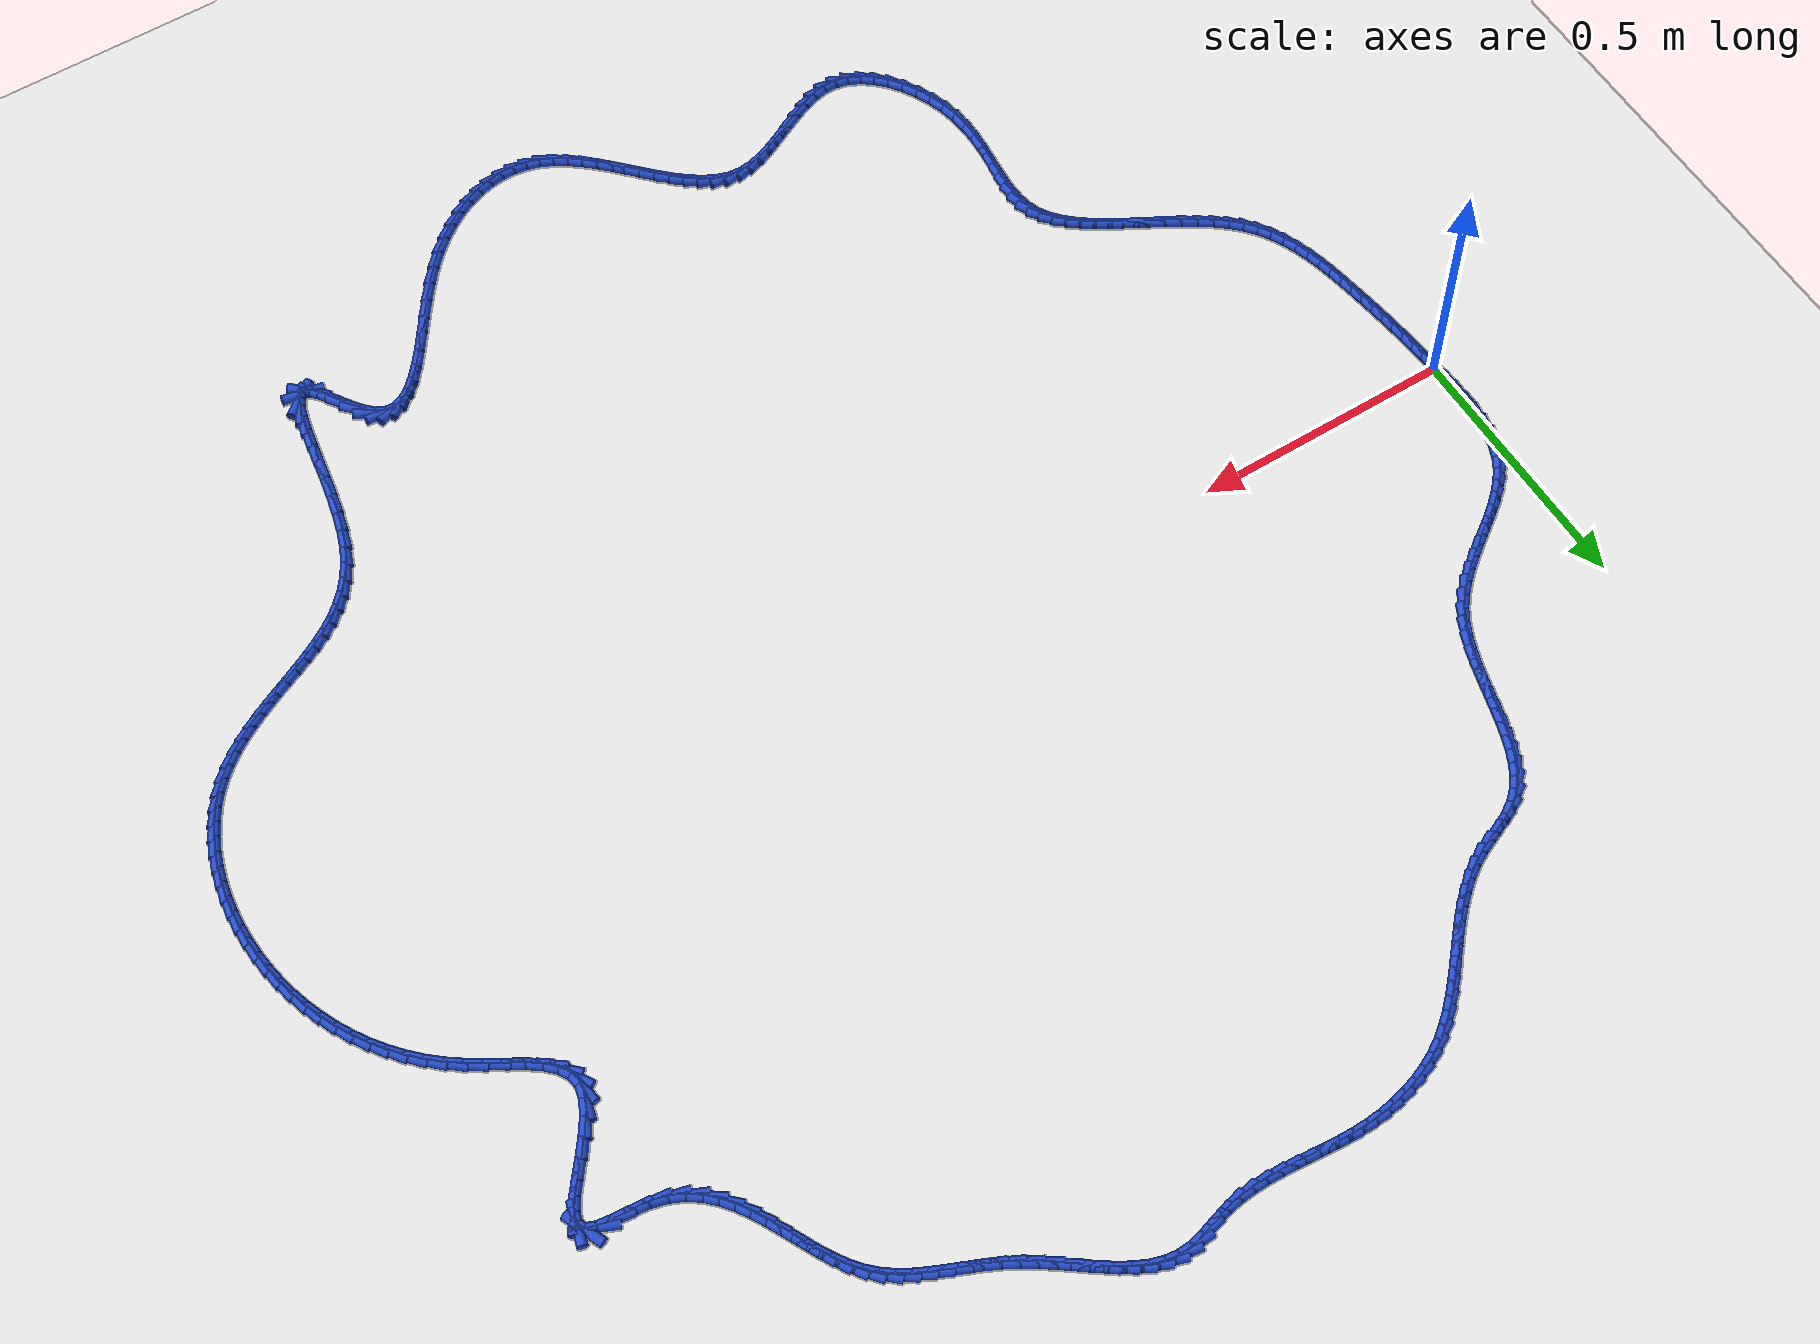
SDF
<sdf version="1.6">
 <world name="default">
  <light name="sun" type="directional">
   <pose>0 0 10 0 -0 0</pose>
   <diffuse>0.8 0.8 0.8 1</diffuse>
   <specular>0.2 0.2 0.2 1</specular>
   <attenuation>
    <range>1000</range>
    <constant>0.9</constant>
    <linear>0.01</linear>
    <quadratic>0.001</quadratic>
   </attenuation>
   <direction>-0.5 0.1 -0.9</direction>
  </light>
  <model name="ground_plane">
   <static>1</static>
   <link name="link">
    <collision name="collision">
     <geometry><plane><normal>0 0 1</normal><size>100 100</size></plane></geometry>
     <surface><friction><ode><mu>100</mu><mu2>50</mu2></ode></friction></surface>
    </collision>
    <visual name="visual">
     <cast_shadows>0</cast_shadows>
     <geometry><plane><normal>0 0 1</normal><size>100 100</size></plane></geometry>
     <material>
      <script><uri>file://media/materials/scripts/gazebo.material</uri><name>Gazebo/WhiteGlow</name></script>
     </material>
    </visual>
   </link>
  </model>
  <gravity>0 0 -9.8</gravity>
  <magnetic_field>6e-06 2.3e-05 -4.2e-05</magnetic_field>
  <atmosphere type="adiabatic"/>
  <physics name="default_physics" default="0" type="ode">
   <max_step_size>0.001</max_step_size>
   <real_time_factor>1</real_time_factor>
   <real_time_update_rate>1000</real_time_update_rate>
  </physics>
  <scene><ambient>0.4 0.4 0.4 1</ambient><background>0.7 0.7 0.7 1</background><shadows>1</shadows></scene>
  <spherical_coordinates>
   <surface_model>EARTH_WGS84</surface_model>
   <latitude_deg>0</latitude_deg>
   <longitude_deg>0</longitude_deg>
   <elevation>0</elevation>
   <heading_deg>0</heading_deg>
  </spherical_coordinates>
  <model name="line">
   <link name="link_0">
    <pose>-1.3877787807814457e-17 -1.3877787807814457e-17 0.01 0 1.57 -1.5056627772746152</pose>
    <collision name="collision">
     <geometry><cylinder><radius>0.01</radius><length>0.08</length></cylinder></geometry>
    </collision>
    <visual name="visual">
     <material>
      <script><name>Gazebo/Blue</name><uri>file://media/materials/scripts/gazebo.material</uri></script>
     </material>
     <geometry><cylinder><radius>0.01</radius><length>0.08</length></cylinder></geometry>
    </visual>
   </link>
   <link name="link_1">
    <pose>-0.0018641513802052682 0.028579963817722043 0.01 0 1.57 -1.526857474830623</pose>
    <collision name="collision">
     <geometry><cylinder><radius>0.01</radius><length>0.08</length></cylinder></geometry>
    </collision>
    <visual name="visual">
     <material>
      <script><name>Gazebo/Blue</name><uri>file://media/materials/scripts/gazebo.material</uri></script>
     </material>
     <geometry><cylinder><radius>0.01</radius><length>0.08</length></cylinder></geometry>
    </visual>
   </link>
   <link name="link_2">
    <pose>-0.003132722673962283 0.05743267057885642 0.01 0 1.57 -1.5605036924303264</pose>
    <collision name="collision">
     <geometry><cylinder><radius>0.01</radius><length>0.08</length></cylinder></geometry>
    </collision>
    <visual name="visual">
     <material>
      <script><name>Gazebo/Blue</name><uri>file://media/materials/scripts/gazebo.material</uri></script>
     </material>
     <geometry><cylinder><radius>0.01</radius><length>0.08</length></cylinder></geometry>
    </visual>
   </link>
   <link name="link_3">
    <pose>-0.0034292147071202234 0.08623788726355473 0.01 0 1.57 1.5338167391921096</pose>
    <collision name="collision">
     <geometry><cylinder><radius>0.01</radius><length>0.08</length></cylinder></geometry>
    </collision>
    <visual name="visual">
     <material>
      <script><name>Gazebo/Blue</name><uri>file://media/materials/scripts/gazebo.material</uri></script>
     </material>
     <geometry><cylinder><radius>0.01</radius><length>0.08</length></cylinder></geometry>
    </visual>
   </link>
   <link name="link_4">
    <pose>-0.0023771283055282616 0.11467538085196868 0.01 0 1.57 1.4710488130899328</pose>
    <collision name="collision">
     <geometry><cylinder><radius>0.01</radius><length>0.08</length></cylinder></geometry>
    </collision>
    <visual name="visual">
     <material>
      <script><name>Gazebo/Blue</name><uri>file://media/materials/scripts/gazebo.material</uri></script>
     </material>
     <geometry><cylinder><radius>0.01</radius><length>0.08</length></cylinder></geometry>
    </visual>
   </link>
   <link name="link_5">
    <pose>0.0004000357049644288 0.14242491832424994 0.01 0 1.57 1.3903391922496144</pose>
    <collision name="collision">
     <geometry><cylinder><radius>0.01</radius><length>0.08</length></cylinder></geometry>
    </collision>
    <visual name="visual">
     <material>
      <script><name>Gazebo/Blue</name><uri>file://media/materials/scripts/gazebo.material</uri></script>
     </material>
     <geometry><cylinder><radius>0.01</radius><length>0.08</length></cylinder></geometry>
    </visual>
   </link>
   <link name="link_6">
    <pose>0.005278776498508688 0.16916626666055012 0.01 0 1.57 1.289008361410767</pose>
    <collision name="collision">
     <geometry><cylinder><radius>0.01</radius><length>0.08</length></cylinder></geometry>
    </collision>
    <visual name="visual">
     <material>
      <script><name>Gazebo/Blue</name><uri>file://media/materials/scripts/gazebo.material</uri></script>
     </material>
     <geometry><cylinder><radius>0.01</radius><length>0.08</length></cylinder></geometry>
    </visual>
   </link>
   <link name="link_7">
    <pose>0.01263559324925534 0.1945791928410209 0.01 0 1.57 1.1649555800092752</pose>
    <collision name="collision">
     <geometry><cylinder><radius>0.01</radius><length>0.08</length></cylinder></geometry>
    </collision>
    <visual name="visual">
     <material>
      <script><name>Gazebo/Blue</name><uri>file://media/materials/scripts/gazebo.material</uri></script>
     </material>
     <geometry><cylinder><radius>0.01</radius><length>0.08</length></cylinder></geometry>
    </visual>
   </link>
   <link name="link_8">
    <pose>0.022846985131355226 0.21834346384581393 0.01 0 1.57 1.0220207684013998</pose>
    <collision name="collision">
     <geometry><cylinder><radius>0.01</radius><length>0.08</length></cylinder></geometry>
    </collision>
    <visual name="visual">
     <material>
      <script><name>Gazebo/Blue</name><uri>file://media/materials/scripts/gazebo.material</uri></script>
     </material>
     <geometry><cylinder><radius>0.01</radius><length>0.08</length></cylinder></geometry>
    </visual>
   </link>
   <link name="link_9">
    <pose>0.03620991123153847 0.24019895994932172 0.01 0 1.57 0.8910838151363568</pose>
    <collision name="collision">
     <geometry><cylinder><radius>0.01</radius><length>0.08</length></cylinder></geometry>
    </collision>
    <visual name="visual">
     <material>
      <script><name>Gazebo/Blue</name><uri>file://media/materials/scripts/gazebo.material</uri></script>
     </material>
     <geometry><cylinder><radius>0.01</radius><length>0.08</length></cylinder></geometry>
    </visual>
   </link>
   <link name="link_10">
    <pose>0.052461989767846745 0.26030828942776263 0.01 0 1.57 0.787225298565199</pose>
    <collision name="collision">
     <geometry><cylinder><radius>0.01</radius><length>0.08</length></cylinder></geometry>
    </collision>
    <visual name="visual">
     <material>
      <script><name>Gazebo/Blue</name><uri>file://media/materials/scripts/gazebo.material</uri></script>
     </material>
     <geometry><cylinder><radius>0.01</radius><length>0.08</length></cylinder></geometry>
    </visual>
   </link>
   <link name="link_11">
    <pose>0.07110087785035743 0.2790154137989366 0.01 0 1.57 0.710278909525239</pose>
    <collision name="collision">
     <geometry><cylinder><radius>0.01</radius><length>0.08</length></cylinder></geometry>
    </collision>
    <visual name="visual">
     <material>
      <script><name>Gazebo/Blue</name><uri>file://media/materials/scripts/gazebo.material</uri></script>
     </material>
     <geometry><cylinder><radius>0.01</radius><length>0.08</length></cylinder></geometry>
    </visual>
   </link>
   <link name="link_12">
    <pose>0.09162331264807584 0.2966649898362074 0.01 0 1.57 0.6582274548759278</pose>
    <collision name="collision">
     <geometry><cylinder><radius>0.01</radius><length>0.08</length></cylinder></geometry>
    </collision>
    <visual name="visual">
     <material>
      <script><name>Gazebo/Blue</name><uri>file://media/materials/scripts/gazebo.material</uri></script>
     </material>
     <geometry><cylinder><radius>0.01</radius><length>0.08</length></cylinder></geometry>
    </visual>
   </link>
   <link name="link_13">
    <pose>0.11352603133000733 0.3136016743129392 0.01 0 1.57 0.6288355130759969</pose>
    <collision name="collision">
     <geometry><cylinder><radius>0.01</radius><length>0.08</length></cylinder></geometry>
    </collision>
    <visual name="visual">
     <material>
      <script><name>Gazebo/Blue</name><uri>file://media/materials/scripts/gazebo.material</uri></script>
     </material>
     <geometry><cylinder><radius>0.01</radius><length>0.08</length></cylinder></geometry>
    </visual>
   </link>
   <link name="link_14">
    <pose>0.13630577106515712 0.33017012400249596 0.01 0 1.57 0.6204398951449394</pose>
    <collision name="collision">
     <geometry><cylinder><radius>0.01</radius><length>0.08</length></cylinder></geometry>
    </collision>
    <visual name="visual">
     <material>
      <script><name>Gazebo/Blue</name><uri>file://media/materials/scripts/gazebo.material</uri></script>
     </material>
     <geometry><cylinder><radius>0.01</radius><length>0.08</length></cylinder></geometry>
    </visual>
   </link>
   <link name="link_15">
    <pose>0.1594592690225307 0.34671499567824166 0.01 0 1.57 0.6322314534657636</pose>
    <collision name="collision">
     <geometry><cylinder><radius>0.01</radius><length>0.08</length></cylinder></geometry>
    </collision>
    <visual name="visual">
     <material>
      <script><name>Gazebo/Blue</name><uri>file://media/materials/scripts/gazebo.material</uri></script>
     </material>
     <geometry><cylinder><radius>0.01</radius><length>0.08</length></cylinder></geometry>
    </visual>
   </link>
   <link name="link_16">
    <pose>0.18248326237113321 0.3635809461135402 0.01 0 1.57 0.6642709617409228</pose>
    <collision name="collision">
     <geometry><cylinder><radius>0.01</radius><length>0.08</length></cylinder></geometry>
    </collision>
    <visual name="visual">
     <material>
      <script><name>Gazebo/Blue</name><uri>file://media/materials/scripts/gazebo.material</uri></script>
     </material>
     <geometry><cylinder><radius>0.01</radius><length>0.08</length></cylinder></geometry>
    </visual>
   </link>
   <link name="link_17">
    <pose>0.20487448827997012 0.38111263208175544 0.01 0 1.57 0.7173300370963076</pose>
    <collision name="collision">
     <geometry><cylinder><radius>0.01</radius><length>0.08</length></cylinder></geometry>
    </collision>
    <visual name="visual">
     <material>
      <script><name>Gazebo/Blue</name><uri>file://media/materials/scripts/gazebo.material</uri></script>
     </material>
     <geometry><cylinder><radius>0.01</radius><length>0.08</length></cylinder></geometry>
    </visual>
   </link>
   <link name="link_18">
    <pose>0.22612968391804666 0.3996547103562516 0.01 0 1.57 0.7925153110881008</pose>
    <collision name="collision">
     <geometry><cylinder><radius>0.01</radius><length>0.08</length></cylinder></geometry>
    </collision>
    <visual name="visual">
     <material>
      <script><name>Gazebo/Blue</name><uri>file://media/materials/scripts/gazebo.material</uri></script>
     </material>
     <geometry><cylinder><radius>0.01</radius><length>0.08</length></cylinder></geometry>
    </visual>
   </link>
   <link name="link_19">
    <pose>0.2457455864543683 0.4195518377103926 0.01 0 1.57 0.8905494043133252</pose>
    <collision name="collision">
     <geometry><cylinder><radius>0.01</radius><length>0.08</length></cylinder></geometry>
    </collision>
    <visual name="visual">
     <material>
      <script><name>Gazebo/Blue</name><uri>file://media/materials/scripts/gazebo.material</uri></script>
     </material>
     <geometry><cylinder><radius>0.01</radius><length>0.08</length></cylinder></geometry>
    </visual>
   </link>
   <link name="link_20">
    <pose>0.2632189330579402 0.4411486709175423 0.01 0 1.57 1.0043668266328554</pose>
    <collision name="collision">
     <geometry><cylinder><radius>0.01</radius><length>0.08</length></cylinder></geometry>
    </collision>
    <visual name="visual">
     <material>
      <script><name>Gazebo/Blue</name><uri>file://media/materials/scripts/gazebo.material</uri></script>
     </material>
     <geometry><cylinder><radius>0.01</radius><length>0.08</length></cylinder></geometry>
    </visual>
   </link>
   <link name="link_21">
    <pose>0.2781854417625283 0.4646830403548929 0.01 0 1.57 1.1040819992891764</pose>
    <collision name="collision">
     <geometry><cylinder><radius>0.01</radius><length>0.08</length></cylinder></geometry>
    </collision>
    <visual name="visual">
     <material>
      <script><name>Gazebo/Blue</name><uri>file://media/materials/scripts/gazebo.material</uri></script>
     </material>
     <geometry><cylinder><radius>0.01</radius><length>0.08</length></cylinder></geometry>
    </visual>
   </link>
   <link name="link_22">
    <pose>0.2908994452443325 0.48991728379866534 0.01 0 1.57 1.1818099463520608</pose>
    <collision name="collision">
     <geometry><cylinder><radius>0.01</radius><length>0.08</length></cylinder></geometry>
    </collision>
    <visual name="visual">
     <material>
      <script><name>Gazebo/Blue</name><uri>file://media/materials/scripts/gazebo.material</uri></script>
     </material>
     <geometry><cylinder><radius>0.01</radius><length>0.08</length></cylinder></geometry>
    </visual>
   </link>
   <link name="link_23">
    <pose>0.3017873306543706 0.5164814908949382 0.01 0 1.57 1.2388330062978474</pose>
    <collision name="collision">
     <geometry><cylinder><radius>0.01</radius><length>0.08</length></cylinder></geometry>
    </collision>
    <visual name="visual">
     <material>
      <script><name>Gazebo/Blue</name><uri>file://media/materials/scripts/gazebo.material</uri></script>
     </material>
     <geometry><cylinder><radius>0.01</radius><length>0.08</length></cylinder></geometry>
    </visual>
   </link>
   <link name="link_24">
    <pose>0.311275492129174 0.5440057459204385 0.01 0 1.57 1.2767142184721187</pose>
    <collision name="collision">
     <geometry><cylinder><radius>0.01</radius><length>0.08</length></cylinder></geometry>
    </collision>
    <visual name="visual">
     <material>
      <script><name>Gazebo/Blue</name><uri>file://media/materials/scripts/gazebo.material</uri></script>
     </material>
     <geometry><cylinder><radius>0.01</radius><length>0.08</length></cylinder></geometry>
    </visual>
   </link>
   <link name="link_25">
    <pose>0.31979032380527445 0.5721201331518927 0.01 0 1.57 1.2966684916331312</pose>
    <collision name="collision">
     <geometry><cylinder><radius>0.01</radius><length>0.08</length></cylinder></geometry>
    </collision>
    <visual name="visual">
     <material>
      <script><name>Gazebo/Blue</name><uri>file://media/materials/scripts/gazebo.material</uri></script>
     </material>
     <geometry><cylinder><radius>0.01</radius><length>0.08</length></cylinder></geometry>
    </visual>
   </link>
   <link name="link_26">
    <pose>0.32775821981920356 0.6004547368660276 0.01 0 1.57 1.2992496240136764</pose>
    <collision name="collision">
     <geometry><cylinder><radius>0.01</radius><length>0.08</length></cylinder></geometry>
    </collision>
    <visual name="visual">
     <material>
      <script><name>Gazebo/Blue</name><uri>file://media/materials/scripts/gazebo.material</uri></script>
     </material>
     <geometry><cylinder><radius>0.01</radius><length>0.08</length></cylinder></geometry>
    </visual>
   </link>
   <link name="link_27">
    <pose>0.3356055743074926 0.6286396413395694 0.01 0 1.57 1.2842007915698364</pose>
    <collision name="collision">
     <geometry><cylinder><radius>0.01</radius><length>0.08</length></cylinder></geometry>
    </collision>
    <visual name="visual">
     <material>
      <script><name>Gazebo/Blue</name><uri>file://media/materials/scripts/gazebo.material</uri></script>
     </material>
     <geometry><cylinder><radius>0.01</radius><length>0.08</length></cylinder></geometry>
    </visual>
   </link>
   <link name="link_28">
    <pose>0.3437587814066733 0.656304930849245 0.01 0 1.57 1.2503841151551327</pose>
    <collision name="collision">
     <geometry><cylinder><radius>0.01</radius><length>0.08</length></cylinder></geometry>
    </collision>
    <visual name="visual">
     <material>
      <script><name>Gazebo/Blue</name><uri>file://media/materials/scripts/gazebo.material</uri></script>
     </material>
     <geometry><cylinder><radius>0.01</radius><length>0.08</length></cylinder></geometry>
    </visual>
   </link>
   <link name="link_29">
    <pose>0.35264423525327737 0.6830806896717811 0.01 0 1.57 1.1957896744040493</pose>
    <collision name="collision">
     <geometry><cylinder><radius>0.01</radius><length>0.08</length></cylinder></geometry>
    </collision>
    <visual name="visual">
     <material>
      <script><name>Gazebo/Blue</name><uri>file://media/materials/scripts/gazebo.material</uri></script>
     </material>
     <geometry><cylinder><radius>0.01</radius><length>0.08</length></cylinder></geometry>
    </visual>
   </link>
   <link name="link_30">
    <pose>0.36268832998383616 0.7085970020839042 0.01 0 1.57 1.1177318025531953</pose>
    <collision name="collision">
     <geometry><cylinder><radius>0.01</radius><length>0.08</length></cylinder></geometry>
    </collision>
    <visual name="visual">
     <material>
      <script><name>Gazebo/Blue</name><uri>file://media/materials/scripts/gazebo.material</uri></script>
     </material>
     <geometry><cylinder><radius>0.01</radius><length>0.08</length></cylinder></geometry>
    </visual>
   </link>
   <link name="link_31">
    <pose>0.37431745973488123 0.732483952362341 0.01 0 1.57 1.0134871277024728</pose>
    <collision name="collision">
     <geometry><cylinder><radius>0.01</radius><length>0.08</length></cylinder></geometry>
    </collision>
    <visual name="visual">
     <material>
      <script><name>Gazebo/Blue</name><uri>file://media/materials/scripts/gazebo.material</uri></script>
     </material>
     <geometry><cylinder><radius>0.01</radius><length>0.08</length></cylinder></geometry>
    </visual>
   </link>
   <link name="link_32">
    <pose>0.3879580186429441 0.7543716247838177 0.01 0 1.57 0.8817394334140569</pose>
    <collision name="collision">
     <geometry><cylinder><radius>0.01</radius><length>0.08</length></cylinder></geometry>
    </collision>
    <visual name="visual">
     <material>
      <script><name>Gazebo/Blue</name><uri>file://media/materials/scripts/gazebo.material</uri></script>
     </material>
     <geometry><cylinder><radius>0.01</radius><length>0.08</length></cylinder></geometry>
    </visual>
   </link>
   <link name="link_33">
    <pose>0.40403640084455655 0.7738901036250615 0.01 0 1.57 0.7249146118301343</pose>
    <collision name="collision">
     <geometry><cylinder><radius>0.01</radius><length>0.08</length></cylinder></geometry>
    </collision>
    <visual name="visual">
     <material>
      <script><name>Gazebo/Blue</name><uri>file://media/materials/scripts/gazebo.material</uri></script>
     </material>
     <geometry><cylinder><radius>0.01</radius><length>0.08</length></cylinder></geometry>
    </visual>
   </link>
   <link name="link_34">
    <pose>0.4229790004762498 0.7906694731627986 0.01 0 1.57 0.5577782972668263</pose>
    <collision name="collision">
     <geometry><cylinder><radius>0.01</radius><length>0.08</length></cylinder></geometry>
    </collision>
    <visual name="visual">
     <material>
      <script><name>Gazebo/Blue</name><uri>file://media/materials/scripts/gazebo.material</uri></script>
     </material>
     <geometry><cylinder><radius>0.01</radius><length>0.08</length></cylinder></geometry>
    </visual>
   </link>
   <link name="link_35">
    <pose>0.4450906025545133 0.8044639919627228 0.01 0 1.57 0.4430533188256063</pose>
    <collision name="collision">
     <geometry><cylinder><radius>0.01</radius><length>0.08</length></cylinder></geometry>
    </collision>
    <visual name="visual">
     <material>
      <script><name>Gazebo/Blue</name><uri>file://media/materials/scripts/gazebo.material</uri></script>
     </material>
     <geometry><cylinder><radius>0.01</radius><length>0.08</length></cylinder></geometry>
    </visual>
   </link>
   <link name="link_36">
    <pose>0.4696217404852276 0.8161044081177452 0.01 0 1.57 0.4006804732066973</pose>
    <collision name="collision">
     <geometry><cylinder><radius>0.01</radius><length>0.08</length></cylinder></geometry>
    </collision>
    <visual name="visual">
     <material>
      <script><name>Gazebo/Blue</name><uri>file://media/materials/scripts/gazebo.material</uri></script>
     </material>
     <geometry><cylinder><radius>0.01</radius><length>0.08</length></cylinder></geometry>
    </visual>
   </link>
   <link name="link_37">
    <pose>0.495281894636061 0.8269739354921776 0.01 0 1.57 0.42330920103418146</pose>
    <collision name="collision">
     <geometry><cylinder><radius>0.01</radius><length>0.08</length></cylinder></geometry>
    </collision>
    <visual name="visual">
     <material>
      <script><name>Gazebo/Blue</name><uri>file://media/materials/scripts/gazebo.material</uri></script>
     </material>
     <geometry><cylinder><radius>0.01</radius><length>0.08</length></cylinder></geometry>
    </visual>
   </link>
   <link name="link_38">
    <pose>0.5207761265441244 0.8384602999897428 0.01 0 1.57 0.5047239543164519</pose>
    <collision name="collision">
     <geometry><cylinder><radius>0.01</radius><length>0.08</length></cylinder></geometry>
    </collision>
    <visual name="visual">
     <material>
      <script><name>Gazebo/Blue</name><uri>file://media/materials/scripts/gazebo.material</uri></script>
     </material>
     <geometry><cylinder><radius>0.01</radius><length>0.08</length></cylinder></geometry>
    </visual>
   </link>
   <link name="link_39">
    <pose>0.5449376407251897 0.8518083818414227 0.01 0 1.57 0.5968045073643752</pose>
    <collision name="collision">
     <geometry><cylinder><radius>0.01</radius><length>0.08</length></cylinder></geometry>
    </collision>
    <visual name="visual">
     <material>
      <script><name>Gazebo/Blue</name><uri>file://media/materials/scripts/gazebo.material</uri></script>
     </material>
     <geometry><cylinder><radius>0.01</radius><length>0.08</length></cylinder></geometry>
    </visual>
   </link>
   <link name="link_40">
    <pose>0.5675673778428116 0.8671842903419158 0.01 0 1.57 0.6748686698634557</pose>
    <collision name="collision">
     <geometry><cylinder><radius>0.01</radius><length>0.08</length></cylinder></geometry>
    </collision>
    <visual name="visual">
     <material>
      <script><name>Gazebo/Blue</name><uri>file://media/materials/scripts/gazebo.material</uri></script>
     </material>
     <geometry><cylinder><radius>0.01</radius><length>0.08</length></cylinder></geometry>
    </visual>
   </link>
   <link name="link_41">
    <pose>0.5889082469518588 0.8842614564289191 0.01 0 1.57 0.7377435125972711</pose>
    <collision name="collision">
     <geometry><cylinder><radius>0.01</radius><length>0.08</length></cylinder></geometry>
    </collision>
    <visual name="visual">
     <material>
      <script><name>Gazebo/Blue</name><uri>file://media/materials/scripts/gazebo.material</uri></script>
     </material>
     <geometry><cylinder><radius>0.01</radius><length>0.08</length></cylinder></geometry>
    </visual>
   </link>
   <link name="link_42">
    <pose>0.6092054243479514 0.9027107836638025 0.01 0 1.57 0.7852373563932779</pose>
    <collision name="collision">
     <geometry><cylinder><radius>0.01</radius><length>0.08</length></cylinder></geometry>
    </collision>
    <visual name="visual">
     <material>
      <script><name>Gazebo/Blue</name><uri>file://media/materials/scripts/gazebo.material</uri></script>
     </material>
     <geometry><cylinder><radius>0.01</radius><length>0.08</length></cylinder></geometry>
    </visual>
   </link>
   <link name="link_43">
    <pose>0.6287040863267105 0.9222031756079367 0.01 0 1.57 0.8175960525939158</pose>
    <collision name="collision">
     <geometry><cylinder><radius>0.01</radius><length>0.08</length></cylinder></geometry>
    </collision>
    <visual name="visual">
     <material>
      <script><name>Gazebo/Blue</name><uri>file://media/materials/scripts/gazebo.material</uri></script>
     </material>
     <geometry><cylinder><radius>0.01</radius><length>0.08</length></cylinder></geometry>
    </visual>
   </link>
   <link name="link_44">
    <pose>0.6476494091837564 0.942409535822691 0.01 0 1.57 0.8351697216548243</pose>
    <collision name="collision">
     <geometry><cylinder><radius>0.01</radius><length>0.08</length></cylinder></geometry>
    </collision>
    <visual name="visual">
     <material>
      <script><name>Gazebo/Blue</name><uri>file://media/materials/scripts/gazebo.material</uri></script>
     </material>
     <geometry><cylinder><radius>0.01</radius><length>0.08</length></cylinder></geometry>
    </visual>
   </link>
   <link name="link_45">
    <pose>0.66628656921471 0.9630007678694362 0.01 0 1.57 0.8381989010319875</pose>
    <collision name="collision">
     <geometry><cylinder><radius>0.01</radius><length>0.08</length></cylinder></geometry>
    </collision>
    <visual name="visual">
     <material>
      <script><name>Gazebo/Blue</name><uri>file://media/materials/scripts/gazebo.material</uri></script>
     </material>
     <geometry><cylinder><radius>0.01</radius><length>0.08</length></cylinder></geometry>
    </visual>
   </link>
   <link name="link_46">
    <pose>0.684860742715192 0.9836477753095424 0.01 0 1.57 0.8267066490759889</pose>
    <collision name="collision">
     <geometry><cylinder><radius>0.01</radius><length>0.08</length></cylinder></geometry>
    </collision>
    <visual name="visual">
     <material>
      <script><name>Gazebo/Blue</name><uri>file://media/materials/scripts/gazebo.material</uri></script>
     </material>
     <geometry><cylinder><radius>0.01</radius><length>0.08</length></cylinder></geometry>
    </visual>
   </link>
   <link name="link_47">
    <pose>0.7036171059808235 1.0040214617043794 0.01 0 1.57 0.8004795410268588</pose>
    <collision name="collision">
     <geometry><cylinder><radius>0.01</radius><length>0.08</length></cylinder></geometry>
    </collision>
    <visual name="visual">
     <material>
      <script><name>Gazebo/Blue</name><uri>file://media/materials/scripts/gazebo.material</uri></script>
     </material>
     <geometry><cylinder><radius>0.01</radius><length>0.08</length></cylinder></geometry>
    </visual>
   </link>
   <link name="link_48">
    <pose>0.7228008353072249 1.0237927306153183 0.01 0 1.57 0.7591349251705215</pose>
    <collision name="collision">
     <geometry><cylinder><radius>0.01</radius><length>0.08</length></cylinder></geometry>
    </collision>
    <visual name="visual">
     <material>
      <script><name>Gazebo/Blue</name><uri>file://media/materials/scripts/gazebo.material</uri></script>
     </material>
     <geometry><cylinder><radius>0.01</radius><length>0.08</length></cylinder></geometry>
    </visual>
   </link>
   <link name="link_49">
    <pose>0.742657106990017 1.0426324856037281 0.01 0 1.57 0.7022892694925332</pose>
    <collision name="collision">
     <geometry><cylinder><radius>0.01</radius><length>0.08</length></cylinder></geometry>
    </collision>
    <visual name="visual">
     <material>
      <script><name>Gazebo/Blue</name><uri>file://media/materials/scripts/gazebo.material</uri></script>
     </material>
     <geometry><cylinder><radius>0.01</radius><length>0.08</length></cylinder></geometry>
    </visual>
   </link>
   <link name="link_50">
    <pose>0.7634310973248204 1.0602116302309796 0.01 0 1.57 0.6298491340203288</pose>
    <collision name="collision">
     <geometry><cylinder><radius>0.01</radius><length>0.08</length></cylinder></geometry>
    </collision>
    <visual name="visual">
     <material>
      <script><name>Gazebo/Blue</name><uri>file://media/materials/scripts/gazebo.material</uri></script>
     </material>
     <geometry><cylinder><radius>0.01</radius><length>0.08</length></cylinder></geometry>
    </visual>
   </link>
   <link name="link_51">
    <pose>0.7853679826072556 1.0762010680584426 0.01 0 1.57 0.5436345084912292</pose>
    <collision name="collision">
     <geometry><cylinder><radius>0.01</radius><length>0.08</length></cylinder></geometry>
    </collision>
    <visual name="visual">
     <material>
      <script><name>Gazebo/Blue</name><uri>file://media/materials/scripts/gazebo.material</uri></script>
     </material>
     <geometry><cylinder><radius>0.01</radius><length>0.08</length></cylinder></geometry>
    </visual>
   </link>
   <link name="link_52">
    <pose>0.8086833155387171 1.0902924094232795 0.01 0 1.57 0.45632815377998504</pose>
    <collision name="collision">
     <geometry><cylinder><radius>0.01</radius><length>0.08</length></cylinder></geometry>
    </collision>
    <visual name="visual">
     <material>
      <script><name>Gazebo/Blue</name><uri>file://media/materials/scripts/gazebo.material</uri></script>
     </material>
     <geometry><cylinder><radius>0.01</radius><length>0.08</length></cylinder></geometry>
    </visual>
   </link>
   <link name="link_53">
    <pose>0.8333046072003384 1.102378604621736 0.01 0 1.57 0.3741257655127779</pose>
    <collision name="collision">
     <geometry><cylinder><radius>0.01</radius><length>0.08</length></cylinder></geometry>
    </collision>
    <visual name="visual">
     <material>
      <script><name>Gazebo/Blue</name><uri>file://media/materials/scripts/gazebo.material</uri></script>
     </material>
     <geometry><cylinder><radius>0.01</radius><length>0.08</length></cylinder></geometry>
    </visual>
   </link>
   <link name="link_54">
    <pose>0.8589971999080522 1.112465959278777 0.01 0 1.57 0.29621777647125097</pose>
    <collision name="collision">
     <geometry><cylinder><radius>0.01</radius><length>0.08</length></cylinder></geometry>
    </collision>
    <visual name="visual">
     <material>
      <script><name>Gazebo/Blue</name><uri>file://media/materials/scripts/gazebo.material</uri></script>
     </material>
     <geometry><cylinder><radius>0.01</radius><length>0.08</length></cylinder></geometry>
    </visual>
   </link>
   <link name="link_55">
    <pose>0.8855246218578622 1.120562047082061 0.01 0 1.57 0.22163352774274542</pose>
    <collision name="collision">
     <geometry><cylinder><radius>0.01</radius><length>0.08</length></cylinder></geometry>
    </collision>
    <visual name="visual">
     <material>
      <script><name>Gazebo/Blue</name><uri>file://media/materials/scripts/gazebo.material</uri></script>
     </material>
     <geometry><cylinder><radius>0.01</radius><length>0.08</length></cylinder></geometry>
    </visual>
   </link>
   <link name="link_56">
    <pose>0.9126504012457706 1.1266744417192462 0.01 0 1.57 0.14935690914547053</pose>
    <collision name="collision">
     <geometry><cylinder><radius>0.01</radius><length>0.08</length></cylinder></geometry>
    </collision>
    <visual name="visual">
     <material>
      <script><name>Gazebo/Blue</name><uri>file://media/materials/scripts/gazebo.material</uri></script>
     </material>
     <geometry><cylinder><radius>0.01</radius><length>0.08</length></cylinder></geometry>
    </visual>
   </link>
   <link name="link_57">
    <pose>0.9401380662677813 1.130810716877991 0.01 0 1.57 0.07841883388084162</pose>
    <collision name="collision">
     <geometry><cylinder><radius>0.01</radius><length>0.08</length></cylinder></geometry>
    </collision>
    <visual name="visual">
     <material>
      <script><name>Gazebo/Blue</name><uri>file://media/materials/scripts/gazebo.material</uri></script>
     </material>
     <geometry><cylinder><radius>0.01</radius><length>0.08</length></cylinder></geometry>
    </visual>
   </link>
   <link name="link_58">
    <pose>0.9677522634258335 1.1329806398324542 0.01 0 1.57 0.013577635960771876</pose>
    <collision name="collision">
     <geometry><cylinder><radius>0.01</radius><length>0.08</length></cylinder></geometry>
    </collision>
    <visual name="visual">
     <material>
      <script><name>Gazebo/Blue</name><uri>file://media/materials/scripts/gazebo.material</uri></script>
     </material>
     <geometry><cylinder><radius>0.01</radius><length>0.08</length></cylinder></geometry>
    </visual>
   </link>
   <link name="link_59">
    <pose>0.9953398503078965 1.1333552370637323 0.01 0 1.57 -0.0356006324384078</pose>
    <collision name="collision">
     <geometry><cylinder><radius>0.01</radius><length>0.08</length></cylinder></geometry>
    </collision>
    <visual name="visual">
     <material>
      <script><name>Gazebo/Blue</name><uri>file://media/materials/scripts/gazebo.material</uri></script>
     </material>
     <geometry><cylinder><radius>0.01</radius><length>0.08</length></cylinder></geometry>
    </visual>
   </link>
   <link name="link_60">
    <pose>1.0228846569137442 1.1323742100402863 0.01 0 1.57 -0.06795273163460823</pose>
    <collision name="collision">
     <geometry><cylinder><radius>0.01</radius><length>0.08</length></cylinder></geometry>
    </collision>
    <visual name="visual">
     <material>
      <script><name>Gazebo/Blue</name><uri>file://media/materials/scripts/gazebo.material</uri></script>
     </material>
     <geometry><cylinder><radius>0.01</radius><length>0.08</length></cylinder></geometry>
    </visual>
   </link>
   <link name="link_61">
    <pose>1.0503834866731274 1.130502707954606 0.01 0 1.57 -0.08347973531880296</pose>
    <collision name="collision">
     <geometry><cylinder><radius>0.01</radius><length>0.08</length></cylinder></geometry>
    </collision>
    <visual name="visual">
     <material>
      <script><name>Gazebo/Blue</name><uri>file://media/materials/scripts/gazebo.material</uri></script>
     </material>
     <geometry><cylinder><radius>0.01</radius><length>0.08</length></cylinder></geometry>
    </visual>
   </link>
   <link name="link_62">
    <pose>1.0778331430157964 1.12820587999918 0.01 0 1.57 -0.0821949855352124</pose>
    <collision name="collision">
     <geometry><cylinder><radius>0.01</radius><length>0.08</length></cylinder></geometry>
    </collision>
    <visual name="visual">
     <material>
      <script><name>Gazebo/Blue</name><uri>file://media/materials/scripts/gazebo.material</uri></script>
     </material>
     <geometry><cylinder><radius>0.01</radius><length>0.08</length></cylinder></geometry>
    </visual>
   </link>
   <link name="link_63">
    <pose>1.105230429371502 1.125948875366498 0.01 0 1.57 -0.06399158496204717</pose>
    <collision name="collision">
     <geometry><cylinder><radius>0.01</radius><length>0.08</length></cylinder></geometry>
    </collision>
    <visual name="visual">
     <material>
      <script><name>Gazebo/Blue</name><uri>file://media/materials/scripts/gazebo.material</uri></script>
     </material>
     <geometry><cylinder><radius>0.01</radius><length>0.08</length></cylinder></geometry>
    </visual>
   </link>
   <link name="link_64">
    <pose>1.1325721491699943 1.1241968432490481 0.01 0 1.57 -0.028651456260452145</pose>
    <collision name="collision">
     <geometry><cylinder><radius>0.01</radius><length>0.08</length></cylinder></geometry>
    </collision>
    <visual name="visual">
     <material>
      <script><name>Gazebo/Blue</name><uri>file://media/materials/scripts/gazebo.material</uri></script>
     </material>
     <geometry><cylinder><radius>0.01</radius><length>0.08</length></cylinder></geometry>
    </visual>
   </link>
   <link name="link_65">
    <pose>1.1598551058410238 1.1234149328393206 0.01 0 1.57 0.0239974703181446</pose>
    <collision name="collision">
     <geometry><cylinder><radius>0.01</radius><length>0.08</length></cylinder></geometry>
    </collision>
    <visual name="visual">
     <material>
      <script><name>Gazebo/Blue</name><uri>file://media/materials/scripts/gazebo.material</uri></script>
     </material>
     <geometry><cylinder><radius>0.01</radius><length>0.08</length></cylinder></geometry>
    </visual>
   </link>
   <link name="link_66">
    <pose>1.1870761028143422 1.1240682933298043 0.01 0 1.57 0.09376590115668865</pose>
    <collision name="collision">
     <geometry><cylinder><radius>0.01</radius><length>0.08</length></cylinder></geometry>
    </collision>
    <visual name="visual">
     <material>
      <script><name>Gazebo/Blue</name><uri>file://media/materials/scripts/gazebo.material</uri></script>
     </material>
     <geometry><cylinder><radius>0.01</radius><length>0.08</length></cylinder></geometry>
    </visual>
   </link>
   <link name="link_67">
    <pose>1.2142319435196987 1.1266220739129875 0.01 0 1.57 0.17965165779725353</pose>
    <collision name="collision">
     <geometry><cylinder><radius>0.01</radius><length>0.08</length></cylinder></geometry>
    </collision>
    <visual name="visual">
     <material>
      <script><name>Gazebo/Blue</name><uri>file://media/materials/scripts/gazebo.material</uri></script>
     </material>
     <geometry><cylinder><radius>0.01</radius><length>0.08</length></cylinder></geometry>
    </visual>
   </link>
   <link name="link_68">
    <pose>1.2413194313868445 1.1315414237813601 0.01 0 1.57 0.26802392747829523</pose>
    <collision name="collision">
     <geometry><cylinder><radius>0.01</radius><length>0.08</length></cylinder></geometry>
    </collision>
    <visual name="visual">
     <material>
      <script><name>Gazebo/Blue</name><uri>file://media/materials/scripts/gazebo.material</uri></script>
     </material>
     <geometry><cylinder><radius>0.01</radius><length>0.08</length></cylinder></geometry>
    </visual>
   </link>
   <link name="link_69">
    <pose>1.2683109290829406 1.1389541491604618 0.01 0 1.57 0.2914446457398157</pose>
    <collision name="collision">
     <geometry><cylinder><radius>0.01</radius><length>0.08</length></cylinder></geometry>
    </collision>
    <visual name="visual">
     <material>
      <script><name>Gazebo/Blue</name><uri>file://media/materials/scripts/gazebo.material</uri></script>
     </material>
     <geometry><cylinder><radius>0.01</radius><length>0.08</length></cylinder></geometry>
    </visual>
   </link>
   <link name="link_70">
    <pose>1.2950326112471406 1.14697029995917 0.01 0 1.57 0.22430005298441646</pose>
    <collision name="collision">
     <geometry><cylinder><radius>0.01</radius><length>0.08</length></cylinder></geometry>
    </collision>
    <visual name="visual">
     <material>
      <script><name>Gazebo/Blue</name><uri>file://media/materials/scripts/gazebo.material</uri></script>
     </material>
     <geometry><cylinder><radius>0.01</radius><length>0.08</length></cylinder></geometry>
    </visual>
   </link>
   <link name="link_71">
    <pose>1.321256536910218 1.1529529968601222 0.01 0 1.57 0.05680049520561192</pose>
    <collision name="collision">
     <geometry><cylinder><radius>0.01</radius><length>0.08</length></cylinder></geometry>
    </collision>
    <visual name="visual">
     <material>
      <script><name>Gazebo/Blue</name><uri>file://media/materials/scripts/gazebo.material</uri></script>
     </material>
     <geometry><cylinder><radius>0.01</radius><length>0.08</length></cylinder></geometry>
    </visual>
   </link>
   <link name="link_72">
    <pose>1.3467704154121236 1.1544037583247533 0.01 0 1.57 -0.14732418766810487</pose>
    <collision name="collision">
     <geometry><cylinder><radius>0.01</radius><length>0.08</length></cylinder></geometry>
    </collision>
    <visual name="visual">
     <material>
      <script><name>Gazebo/Blue</name><uri>file://media/materials/scripts/gazebo.material</uri></script>
     </material>
     <geometry><cylinder><radius>0.01</radius><length>0.08</length></cylinder></geometry>
    </visual>
   </link>
   <link name="link_73">
    <pose>1.371575976507996 1.1507226283115934 0.01 0 1.57 -0.3202163878088802</pose>
    <collision name="collision">
     <geometry><cylinder><radius>0.01</radius><length>0.08</length></cylinder></geometry>
    </collision>
    <visual name="visual">
     <material>
      <script><name>Gazebo/Blue</name><uri>file://media/materials/scripts/gazebo.material</uri></script>
     </material>
     <geometry><cylinder><radius>0.01</radius><length>0.08</length></cylinder></geometry>
    </visual>
   </link>
   <link name="link_74">
    <pose>1.395829371145521 1.1426794853862428 0.01 0 1.57 -0.45267663990264106</pose>
    <collision name="collision">
     <geometry><cylinder><radius>0.01</radius><length>0.08</length></cylinder></geometry>
    </collision>
    <visual name="visual">
     <material>
      <script><name>Gazebo/Blue</name><uri>file://media/materials/scripts/gazebo.material</uri></script>
     </material>
     <geometry><cylinder><radius>0.01</radius><length>0.08</length></cylinder></geometry>
    </visual>
   </link>
   <link name="link_75">
    <pose>1.4196901689483974 1.1310745343968125 0.01 0 1.57 -0.5463079709869142</pose>
    <collision name="collision">
     <geometry><cylinder><radius>0.01</radius><length>0.08</length></cylinder></geometry>
    </collision>
    <visual name="visual">
     <material>
      <script><name>Gazebo/Blue</name><uri>file://media/materials/scripts/gazebo.material</uri></script>
     </material>
     <geometry><cylinder><radius>0.01</radius><length>0.08</length></cylinder></geometry>
    </visual>
   </link>
   <link name="link_76">
    <pose>1.443317939540323 1.116707980191414 0.01 0 1.57 -0.60615055954736</pose>
    <collision name="collision">
     <geometry><cylinder><radius>0.01</radius><length>0.08</length></cylinder></geometry>
    </collision>
    <visual name="visual">
     <material>
      <script><name>Gazebo/Blue</name><uri>file://media/materials/scripts/gazebo.material</uri></script>
     </material>
     <geometry><cylinder><radius>0.01</radius><length>0.08</length></cylinder></geometry>
    </visual>
   </link>
   <link name="link_77">
    <pose>1.4668722525449958 1.1003800276181572 0.01 0 1.57 -0.636939981395557</pose>
    <collision name="collision">
     <geometry><cylinder><radius>0.01</radius><length>0.08</length></cylinder></geometry>
    </collision>
    <visual name="visual">
     <material>
      <script><name>Gazebo/Blue</name><uri>file://media/materials/scripts/gazebo.material</uri></script>
     </material>
     <geometry><cylinder><radius>0.01</radius><length>0.08</length></cylinder></geometry>
    </visual>
   </link>
   <link name="link_78">
    <pose>1.4905126775861142 1.0828908815251537 0.01 0 1.57 -0.6417721367929571</pose>
    <collision name="collision">
     <geometry><cylinder><radius>0.01</radius><length>0.08</length></cylinder></geometry>
    </collision>
    <visual name="visual">
     <material>
      <script><name>Gazebo/Blue</name><uri>file://media/materials/scripts/gazebo.material</uri></script>
     </material>
     <geometry><cylinder><radius>0.01</radius><length>0.08</length></cylinder></geometry>
    </visual>
   </link>
   <link name="link_79">
    <pose>1.5143987842873752 1.0650407467605152 0.01 0 1.57 -0.621881728110758</pose>
    <collision name="collision">
     <geometry><cylinder><radius>0.01</radius><length>0.08</length></cylinder></geometry>
    </collision>
    <visual name="visual">
     <material>
      <script><name>Gazebo/Blue</name><uri>file://media/materials/scripts/gazebo.material</uri></script>
     </material>
     <geometry><cylinder><radius>0.01</radius><length>0.08</length></cylinder></geometry>
    </visual>
   </link>
   <link name="link_80">
    <pose>1.5386901422724772 1.0476298281723515 0.01 0 1.57 -0.576798807724816</pose>
    <collision name="collision">
     <geometry><cylinder><radius>0.01</radius><length>0.08</length></cylinder></geometry>
    </collision>
    <visual name="visual">
     <material>
      <script><name>Gazebo/Blue</name><uri>file://media/materials/scripts/gazebo.material</uri></script>
     </material>
     <geometry><cylinder><radius>0.01</radius><length>0.08</length></cylinder></geometry>
    </visual>
   </link>
   <link name="link_81">
    <pose>1.5635463211651184 1.031458330608774 0.01 0 1.57 -0.5095774138339798</pose>
    <collision name="collision">
     <geometry><cylinder><radius>0.01</radius><length>0.08</length></cylinder></geometry>
    </collision>
    <visual name="visual">
     <material>
      <script><name>Gazebo/Blue</name><uri>file://media/materials/scripts/gazebo.material</uri></script>
     </material>
     <geometry><cylinder><radius>0.01</radius><length>0.08</length></cylinder></geometry>
    </visual>
   </link>
   <link name="link_82">
    <pose>1.5890764207866805 1.0171920077761607 0.01 0 1.57 -0.4516879873389002</pose>
    <collision name="collision">
     <geometry><cylinder><radius>0.01</radius><length>0.08</length></cylinder></geometry>
    </collision>
    <visual name="visual">
     <material>
      <script><name>Gazebo/Blue</name><uri>file://media/materials/scripts/gazebo.material</uri></script>
     </material>
     <geometry><cylinder><radius>0.01</radius><length>0.08</length></cylinder></geometry>
    </visual>
   </link>
   <link name="link_83">
    <pose>1.6150497275559288 1.0045913532478732 0.01 0 1.57 -0.4173337428751883</pose>
    <collision name="collision">
     <geometry><cylinder><radius>0.01</radius><length>0.08</length></cylinder></geometry>
    </collision>
    <visual name="visual">
     <material>
      <script><name>Gazebo/Blue</name><uri>file://media/materials/scripts/gazebo.material</uri></script>
     </material>
     <geometry><cylinder><radius>0.01</radius><length>0.08</length></cylinder></geometry>
    </visual>
   </link>
   <link name="link_84">
    <pose>1.641095304951707 0.9930433078289995 0.01 0 1.57 -0.4073654501644141</pose>
    <collision name="collision">
     <geometry><cylinder><radius>0.01</radius><length>0.08</length></cylinder></geometry>
    </collision>
    <visual name="visual">
     <material>
      <script><name>Gazebo/Blue</name><uri>file://media/materials/scripts/gazebo.material</uri></script>
     </material>
     <geometry><cylinder><radius>0.01</radius><length>0.08</length></cylinder></geometry>
    </visual>
   </link>
   <link name="link_85">
    <pose>1.666841776290135 0.9819336397347158 0.01 0 1.57 -0.42289795561225374</pose>
    <collision name="collision">
     <geometry><cylinder><radius>0.01</radius><length>0.08</length></cylinder></geometry>
    </collision>
    <visual name="visual">
     <material>
      <script><name>Gazebo/Blue</name><uri>file://media/materials/scripts/gazebo.material</uri></script>
     </material>
     <geometry><cylinder><radius>0.01</radius><length>0.08</length></cylinder></geometry>
    </visual>
   </link>
   <link name="link_86">
    <pose>1.6919177648873316 0.9706481171801985 0.01 0 1.57 -0.4655944123026897</pose>
    <collision name="collision">
     <geometry><cylinder><radius>0.01</radius><length>0.08</length></cylinder></geometry>
    </collision>
    <visual name="visual">
     <material>
      <script><name>Gazebo/Blue</name><uri>file://media/materials/scripts/gazebo.material</uri></script>
     </material>
     <geometry><cylinder><radius>0.01</radius><length>0.08</length></cylinder></geometry>
    </visual>
   </link>
   <link name="link_87">
    <pose>1.715951894059416 0.9585725083806228 0.01 0 1.57 -0.5374037986020508</pose>
    <collision name="collision">
     <geometry><cylinder><radius>0.01</radius><length>0.08</length></cylinder></geometry>
    </collision>
    <visual name="visual">
     <material>
      <script><name>Gazebo/Blue</name><uri>file://media/materials/scripts/gazebo.material</uri></script>
     </material>
     <geometry><cylinder><radius>0.01</radius><length>0.08</length></cylinder></geometry>
    </visual>
   </link>
   <link name="link_88">
    <pose>1.7385727871225058 0.9450925815511648 0.01 0 1.57 -0.6395352327221191</pose>
    <collision name="collision">
     <geometry><cylinder><radius>0.01</radius><length>0.08</length></cylinder></geometry>
    </collision>
    <visual name="visual">
     <material>
      <script><name>Gazebo/Blue</name><uri>file://media/materials/scripts/gazebo.material</uri></script>
     </material>
     <geometry><cylinder><radius>0.01</radius><length>0.08</length></cylinder></geometry>
    </visual>
   </link>
   <link name="link_89">
    <pose>1.7594090673927214 0.9295941049070011 0.01 0 1.57 -0.7701876874329247</pose>
    <collision name="collision">
     <geometry><cylinder><radius>0.01</radius><length>0.08</length></cylinder></geometry>
    </collision>
    <visual name="visual">
     <material>
      <script><name>Gazebo/Blue</name><uri>file://media/materials/scripts/gazebo.material</uri></script>
     </material>
     <geometry><cylinder><radius>0.01</radius><length>0.08</length></cylinder></geometry>
    </visual>
   </link>
   <link name="link_90">
    <pose>1.7780939418413382 0.9114691683862071 0.01 0 1.57 -0.9034623496639498</pose>
    <collision name="collision">
     <geometry><cylinder><radius>0.01</radius><length>0.08</length></cylinder></geometry>
    </collision>
    <visual name="visual">
     <material>
      <script><name>Gazebo/Blue</name><uri>file://media/materials/scripts/gazebo.material</uri></script>
     </material>
     <geometry><cylinder><radius>0.01</radius><length>0.08</length></cylinder></geometry>
    </visual>
   </link>
   <link name="link_91">
    <pose>1.7945782645540493 0.8905479570645414 0.01 0 1.57 -1.0038426076547085</pose>
    <collision name="collision">
     <geometry><cylinder><radius>0.01</radius><length>0.08</length></cylinder></geometry>
    </collision>
    <visual name="visual">
     <material>
      <script><name>Gazebo/Blue</name><uri>file://media/materials/scripts/gazebo.material</uri></script>
     </material>
     <geometry><cylinder><radius>0.01</radius><length>0.08</length></cylinder></geometry>
    </visual>
   </link>
   <link name="link_92">
    <pose>1.809331456283168 0.8673758570219618 0.01 0 1.57 -1.0712734278921052</pose>
    <collision name="collision">
     <geometry><cylinder><radius>0.01</radius><length>0.08</length></cylinder></geometry>
    </collision>
    <visual name="visual">
     <material>
      <script><name>Gazebo/Blue</name><uri>file://media/materials/scripts/gazebo.material</uri></script>
     </material>
     <geometry><cylinder><radius>0.01</radius><length>0.08</length></cylinder></geometry>
    </visual>
   </link>
   <link name="link_93">
    <pose>1.8228707566699627 0.8425642055836581 0.01 0 1.57 -1.1095442872445158</pose>
    <collision name="collision">
     <geometry><cylinder><radius>0.01</radius><length>0.08</length></cylinder></geometry>
    </collision>
    <visual name="visual">
     <material>
      <script><name>Gazebo/Blue</name><uri>file://media/materials/scripts/gazebo.material</uri></script>
     </material>
     <geometry><cylinder><radius>0.01</radius><length>0.08</length></cylinder></geometry>
    </visual>
   </link>
   <link name="link_94">
    <pose>1.8357134053557007 0.8167243400748195 0.01 0 1.57 -1.1214207741752051</pose>
    <collision name="collision">
     <geometry><cylinder><radius>0.01</radius><length>0.08</length></cylinder></geometry>
    </collision>
    <visual name="visual">
     <material>
      <script><name>Gazebo/Blue</name><uri>file://media/materials/scripts/gazebo.material</uri></script>
     </material>
     <geometry><cylinder><radius>0.01</radius><length>0.08</length></cylinder></geometry>
    </visual>
   </link>
   <link name="link_95">
    <pose>1.8483766419816516 0.7904675978206364 0.01 0 1.57 -1.1080723671258257</pose>
    <collision name="collision">
     <geometry><cylinder><radius>0.01</radius><length>0.08</length></cylinder></geometry>
    </collision>
    <visual name="visual">
     <material>
      <script><name>Gazebo/Blue</name><uri>file://media/materials/scripts/gazebo.material</uri></script>
     </material>
     <geometry><cylinder><radius>0.01</radius><length>0.08</length></cylinder></geometry>
    </visual>
   </link>
   <link name="link_96">
    <pose>1.861377706189082 0.7644053161462986 0.01 0 1.57 -1.069015690051241</pose>
    <collision name="collision">
     <geometry><cylinder><radius>0.01</radius><length>0.08</length></cylinder></geometry>
    </collision>
    <visual name="visual">
     <material>
      <script><name>Gazebo/Blue</name><uri>file://media/materials/scripts/gazebo.material</uri></script>
     </material>
     <geometry><cylinder><radius>0.01</radius><length>0.08</length></cylinder></geometry>
    </visual>
   </link>
   <link name="link_97">
    <pose>1.8752338376192605 0.7391488323769961 0.01 0 1.57 -1.002339002714773</pose>
    <collision name="collision">
     <geometry><cylinder><radius>0.01</radius><length>0.08</length></cylinder></geometry>
    </collision>
    <visual name="visual">
     <material>
      <script><name>Gazebo/Blue</name><uri>file://media/materials/scripts/gazebo.material</uri></script>
     </material>
     <geometry><cylinder><radius>0.01</radius><length>0.08</length></cylinder></geometry>
    </visual>
   </link>
   <link name="link_98">
    <pose>1.890462275913455 0.7153094838379189 0.01 0 1.57 -0.9053696773807592</pose>
    <collision name="collision">
     <geometry><cylinder><radius>0.01</radius><length>0.08</length></cylinder></geometry>
    </collision>
    <visual name="visual">
     <material>
      <script><name>Gazebo/Blue</name><uri>file://media/materials/scripts/gazebo.material</uri></script>
     </material>
     <geometry><cylinder><radius>0.01</radius><length>0.08</length></cylinder></geometry>
    </visual>
   </link>
   <link name="link_99">
    <pose>1.9075802607129335 0.6934986078542564 0.01 0 1.57 -0.7762577746734833</pose>
    <collision name="collision">
     <geometry><cylinder><radius>0.01</radius><length>0.08</length></cylinder></geometry>
    </collision>
    <visual name="visual">
     <material>
      <script><name>Gazebo/Blue</name><uri>file://media/materials/scripts/gazebo.material</uri></script>
     </material>
     <geometry><cylinder><radius>0.01</radius><length>0.08</length></cylinder></geometry>
    </visual>
   </link>
   <link name="link_100">
    <pose>1.9271050316589653 0.6743275417511989 0.01 0 1.57 -0.6168510560199968</pose>
    <collision name="collision">
     <geometry><cylinder><radius>0.01</radius><length>0.08</length></cylinder></geometry>
    </collision>
    <visual name="visual">
     <material>
      <script><name>Gazebo/Blue</name><uri>file://media/materials/scripts/gazebo.material</uri></script>
     </material>
     <geometry><cylinder><radius>0.01</radius><length>0.08</length></cylinder></geometry>
    </visual>
   </link>
   <link name="link_101">
    <pose>1.9495538283928173 0.6584076228539365 0.01 0 1.57 -0.4358467954528984</pose>
    <collision name="collision">
     <geometry><cylinder><radius>0.01</radius><length>0.08</length></cylinder></geometry>
    </collision>
    <visual name="visual">
     <material>
      <script><name>Gazebo/Blue</name><uri>file://media/materials/scripts/gazebo.material</uri></script>
     </material>
     <geometry><cylinder><radius>0.01</radius><length>0.08</length></cylinder></geometry>
    </visual>
   </link>
   <link name="link_102">
    <pose>1.975443890555757 0.6463501884876587 0.01 0 1.57 -0.2500680511181714</pose>
    <collision name="collision">
     <geometry><cylinder><radius>0.01</radius><length>0.08</length></cylinder></geometry>
    </collision>
    <visual name="visual">
     <material>
      <script><name>Gazebo/Blue</name><uri>file://media/materials/scripts/gazebo.material</uri></script>
     </material>
     <geometry><cylinder><radius>0.01</radius><length>0.08</length></cylinder></geometry>
    </visual>
   </link>
   <link name="link_103">
    <pose>2.0052506085270636 0.63873712318815 0.01 0 1.57 -0.11830283851813377</pose>
    <collision name="collision">
     <geometry><cylinder><radius>0.01</radius><length>0.08</length></cylinder></geometry>
    </collision>
    <visual name="visual">
     <material>
      <script><name>Gazebo/Blue</name><uri>file://media/materials/scripts/gazebo.material</uri></script>
     </material>
     <geometry><cylinder><radius>0.01</radius><length>0.08</length></cylinder></geometry>
    </visual>
   </link>
   <link name="link_104">
    <pose>2.0376527437870333 0.6348858750331817 0.01 0 1.57 -0.07944997966516416</pose>
    <collision name="collision">
     <geometry><cylinder><radius>0.01</radius><length>0.08</length></cylinder></geometry>
    </collision>
    <visual name="visual">
     <material>
      <script><name>Gazebo/Blue</name><uri>file://media/materials/scripts/gazebo.material</uri></script>
     </material>
     <geometry><cylinder><radius>0.01</radius><length>0.08</length></cylinder></geometry>
    </visual>
   </link>
   <link name="link_105">
    <pose>2.068891934194189 0.6323986864941795 0.01 0 1.57 -0.1384559685129104</pose>
    <collision name="collision">
     <geometry><cylinder><radius>0.01</radius><length>0.08</length></cylinder></geometry>
    </collision>
    <visual name="visual">
     <material>
      <script><name>Gazebo/Blue</name><uri>file://media/materials/scripts/gazebo.material</uri></script>
     </material>
     <geometry><cylinder><radius>0.01</radius><length>0.08</length></cylinder></geometry>
    </visual>
   </link>
   <link name="link_106">
    <pose>2.0950361245145595 0.628755557837303 0.01 0 1.57 -0.4040600202982624</pose>
    <collision name="collision">
     <geometry><cylinder><radius>0.01</radius><length>0.08</length></cylinder></geometry>
    </collision>
    <visual name="visual">
     <material>
      <script><name>Gazebo/Blue</name><uri>file://media/materials/scripts/gazebo.material</uri></script>
     </material>
     <geometry><cylinder><radius>0.01</radius><length>0.08</length></cylinder></geometry>
    </visual>
   </link>
   <link name="link_107">
    <pose>2.1121532595141743 0.6214364893287121 0.01 0 1.57 -1.193388404743611</pose>
    <collision name="collision">
     <geometry><cylinder><radius>0.01</radius><length>0.08</length></cylinder></geometry>
    </collision>
    <visual name="visual">
     <material>
      <script><name>Gazebo/Blue</name><uri>file://media/materials/scripts/gazebo.material</uri></script>
     </material>
     <geometry><cylinder><radius>0.01</radius><length>0.08</length></cylinder></geometry>
    </visual>
   </link>
   <link name="link_108">
    <pose>2.117296949986357 0.6084608139139248 0.01 0 1.57 1.2818512479314532</pose>
    <collision name="collision">
     <geometry><cylinder><radius>0.01</radius><length>0.08</length></cylinder></geometry>
    </collision>
    <visual name="visual">
     <material>
      <script><name>Gazebo/Blue</name><uri>file://media/materials/scripts/gazebo.material</uri></script>
     </material>
     <geometry><cylinder><radius>0.01</radius><length>0.08</length></cylinder></geometry>
    </visual>
   </link>
   <link name="link_109">
    <pose>2.111878214109434 0.590232132774277 0.01 0 1.57 1.0331770734157517</pose>
    <collision name="collision">
     <geometry><cylinder><radius>0.01</radius><length>0.08</length></cylinder></geometry>
    </collision>
    <visual name="visual">
     <material>
      <script><name>Gazebo/Blue</name><uri>file://media/materials/scripts/gazebo.material</uri></script>
     </material>
     <geometry><cylinder><radius>0.01</radius><length>0.08</length></cylinder></geometry>
    </visual>
   </link>
   <link name="link_110">
    <pose>2.098511787588018 0.5678126922920805 0.01 0 1.57 0.9389595610371577</pose>
    <collision name="collision">
     <geometry><cylinder><radius>0.01</radius><length>0.08</length></cylinder></geometry>
    </collision>
    <visual name="visual">
     <material>
      <script><name>Gazebo/Blue</name><uri>file://media/materials/scripts/gazebo.material</uri></script>
     </material>
     <geometry><cylinder><radius>0.01</radius><length>0.08</length></cylinder></geometry>
    </visual>
   </link>
   <link name="link_111">
    <pose>2.0798124464862324 0.5422647609333977 0.01 0 1.57 0.9111128262575541</pose>
    <collision name="collision">
     <geometry><cylinder><radius>0.01</radius><length>0.08</length></cylinder></geometry>
    </collision>
    <visual name="visual">
     <material>
      <script><name>Gazebo/Blue</name><uri>file://media/materials/scripts/gazebo.material</uri></script>
     </material>
     <geometry><cylinder><radius>0.01</radius><length>0.08</length></cylinder></geometry>
    </visual>
   </link>
   <link name="link_112">
    <pose>2.0583949668682036 0.5146506071642912 0.01 0 1.57 0.9260158867525837</pose>
    <collision name="collision">
     <geometry><cylinder><radius>0.01</radius><length>0.08</length></cylinder></geometry>
    </collision>
    <visual name="visual">
     <material>
      <script><name>Gazebo/Blue</name><uri>file://media/materials/scripts/gazebo.material</uri></script>
     </material>
     <geometry><cylinder><radius>0.01</radius><length>0.08</length></cylinder></geometry>
    </visual>
   </link>
   <link name="link_113">
    <pose>2.0368741247980524 0.48603249945082283 0.01 0 1.57 0.9835318177837018</pose>
    <collision name="collision">
     <geometry><cylinder><radius>0.01</radius><length>0.08</length></cylinder></geometry>
    </collision>
    <visual name="visual">
     <material>
      <script><name>Gazebo/Blue</name><uri>file://media/materials/scripts/gazebo.material</uri></script>
     </material>
     <geometry><cylinder><radius>0.01</radius><length>0.08</length></cylinder></geometry>
    </visual>
   </link>
   <link name="link_114">
    <pose>2.0178646963399056 0.45747270625905606 0.01 0 1.57 1.1023893083673468</pose>
    <collision name="collision">
     <geometry><cylinder><radius>0.01</radius><length>0.08</length></cylinder></geometry>
    </collision>
    <visual name="visual">
     <material>
      <script><name>Gazebo/Blue</name><uri>file://media/materials/scripts/gazebo.material</uri></script>
     </material>
     <geometry><cylinder><radius>0.01</radius><length>0.08</length></cylinder></geometry>
    </visual>
   </link>
   <link name="link_115">
    <pose>2.0039814575578863 0.430033496055053 0.01 0 1.57 1.332212132269377</pose>
    <collision name="collision">
     <geometry><cylinder><radius>0.01</radius><length>0.08</length></cylinder></geometry>
    </collision>
    <visual name="visual">
     <material>
      <script><name>Gazebo/Blue</name><uri>file://media/materials/scripts/gazebo.material</uri></script>
     </material>
     <geometry><cylinder><radius>0.01</radius><length>0.08</length></cylinder></geometry>
    </visual>
   </link>
   <link name="link_116">
    <pose>1.9978386366830383 0.40477691344199107 0.01 0 1.57 -1.424916084982434</pose>
    <collision name="collision">
     <geometry><cylinder><radius>0.01</radius><length>0.08</length></cylinder></geometry>
    </collision>
    <visual name="visual">
     <material>
      <script><name>Gazebo/Blue</name><uri>file://media/materials/scripts/gazebo.material</uri></script>
     </material>
     <geometry><cylinder><radius>0.01</radius><length>0.08</length></cylinder></geometry>
    </visual>
   </link>
   <link name="link_117">
    <pose>2.0011280909634643 0.3823880914475904 0.01 0 1.57 -1.0446541489747752</pose>
    <collision name="collision">
     <geometry><cylinder><radius>0.01</radius><length>0.08</length></cylinder></geometry>
    </collision>
    <visual name="visual">
     <material>
      <script><name>Gazebo/Blue</name><uri>file://media/materials/scripts/gazebo.material</uri></script>
     </material>
     <geometry><cylinder><radius>0.01</radius><length>0.08</length></cylinder></geometry>
    </visual>
   </link>
   <link name="link_118">
    <pose>2.012733423345892 0.3624046166431127 0.01 0 1.57 -0.7850106930269752</pose>
    <collision name="collision">
     <geometry><cylinder><radius>0.01</radius><length>0.08</length></cylinder></geometry>
    </collision>
    <visual name="visual">
     <material>
      <script><name>Gazebo/Blue</name><uri>file://media/materials/scripts/gazebo.material</uri></script>
     </material>
     <geometry><cylinder><radius>0.01</radius><length>0.08</length></cylinder></geometry>
    </visual>
   </link>
   <link name="link_119">
    <pose>2.0310057221201414 0.34414647233388673 0.01 0 1.57 -0.6364588288066718</pose>
    <collision name="collision">
     <geometry><cylinder><radius>0.01</radius><length>0.08</length></cylinder></geometry>
    </collision>
    <visual name="visual">
     <material>
      <script><name>Gazebo/Blue</name><uri>file://media/materials/scripts/gazebo.material</uri></script>
     </material>
     <geometry><cylinder><radius>0.01</radius><length>0.08</length></cylinder></geometry>
    </visual>
   </link>
   <link name="link_120">
    <pose>2.0542960755760333 0.326933641825242 0.01 0 1.57 -0.5635831971443453</pose>
    <collision name="collision">
     <geometry><cylinder><radius>0.01</radius><length>0.08</length></cylinder></geometry>
    </collision>
    <visual name="visual">
     <material>
      <script><name>Gazebo/Blue</name><uri>file://media/materials/scripts/gazebo.material</uri></script>
     </material>
     <geometry><cylinder><radius>0.01</radius><length>0.08</length></cylinder></geometry>
    </visual>
   </link>
   <link name="link_121">
    <pose>2.0809555720033894 0.3100861084225077 0.01 0 1.57 -0.5438948360235875</pose>
    <collision name="collision">
     <geometry><cylinder><radius>0.01</radius><length>0.08</length></cylinder></geometry>
    </collision>
    <visual name="visual">
     <material>
      <script><name>Gazebo/Blue</name><uri>file://media/materials/scripts/gazebo.material</uri></script>
     </material>
     <geometry><cylinder><radius>0.01</radius><length>0.08</length></cylinder></geometry>
    </visual>
   </link>
   <link name="link_122">
    <pose>2.109335299692031 0.292923855431013 0.01 0 1.57 -0.5680234738807505</pose>
    <collision name="collision">
     <geometry><cylinder><radius>0.01</radius><length>0.08</length></cylinder></geometry>
    </collision>
    <visual name="visual">
     <material>
      <script><name>Gazebo/Blue</name><uri>file://media/materials/scripts/gazebo.material</uri></script>
     </material>
     <geometry><cylinder><radius>0.01</radius><length>0.08</length></cylinder></geometry>
    </visual>
   </link>
   <link name="link_123">
    <pose>2.137786346931776 0.27476686615608764 0.01 0 1.57 -0.6326325850215475</pose>
    <collision name="collision">
     <geometry><cylinder><radius>0.01</radius><length>0.08</length></cylinder></geometry>
    </collision>
    <visual name="visual">
     <material>
      <script><name>Gazebo/Blue</name><uri>file://media/materials/scripts/gazebo.material</uri></script>
     </material>
     <geometry><cylinder><radius>0.01</radius><length>0.08</length></cylinder></geometry>
    </visual>
   </link>
   <link name="link_124">
    <pose>2.164764773303708 0.2549875092481313 0.01 0 1.57 -0.7117666029238326</pose>
    <collision name="collision">
     <geometry><cylinder><radius>0.01</radius><length>0.08</length></cylinder></geometry>
    </collision>
    <visual name="visual">
     <material>
      <script><name>Gazebo/Blue</name><uri>file://media/materials/scripts/gazebo.material</uri></script>
     </material>
     <geometry><cylinder><radius>0.01</radius><length>0.08</length></cylinder></geometry>
    </visual>
   </link>
   <link name="link_125">
    <pose>2.1897252279711985 0.2334564939916673 0.01 0 1.57 -0.789445883774655</pose>
    <collision name="collision">
     <geometry><cylinder><radius>0.01</radius><length>0.08</length></cylinder></geometry>
    </collision>
    <visual name="visual">
     <material>
      <script><name>Gazebo/Blue</name><uri>file://media/materials/scripts/gazebo.material</uri></script>
     </material>
     <geometry><cylinder><radius>0.01</radius><length>0.08</length></cylinder></geometry>
    </visual>
   </link>
   <link name="link_126">
    <pose>2.2126749043052323 0.21032027381644947 0.01 0 1.57 -0.8651539443826302</pose>
    <collision name="collision">
     <geometry><cylinder><radius>0.01</radius><length>0.08</length></cylinder></geometry>
    </collision>
    <visual name="visual">
     <material>
      <script><name>Gazebo/Blue</name><uri>file://media/materials/scripts/gazebo.material</uri></script>
     </material>
     <geometry><cylinder><radius>0.01</radius><length>0.08</length></cylinder></geometry>
    </visual>
   </link>
   <link name="link_127">
    <pose>2.2336268408564317 0.18572821915695525 0.01 0 1.57 -0.9386758037250155</pose>
    <collision name="collision">
     <geometry><cylinder><radius>0.01</radius><length>0.08</length></cylinder></geometry>
    </collision>
    <visual name="visual">
     <material>
      <script><name>Gazebo/Blue</name><uri>file://media/materials/scripts/gazebo.material</uri></script>
     </material>
     <geometry><cylinder><radius>0.01</radius><length>0.08</length></cylinder></geometry>
    </visual>
   </link>
   <link name="link_128">
    <pose>2.2525940761754213 0.1598297004476612 0.01 0 1.57 -1.009919418727432</pose>
    <collision name="collision">
     <geometry><cylinder><radius>0.01</radius><length>0.08</length></cylinder></geometry>
    </collision>
    <visual name="visual">
     <material>
      <script><name>Gazebo/Blue</name><uri>file://media/materials/scripts/gazebo.material</uri></script>
     </material>
     <geometry><cylinder><radius>0.01</radius><length>0.08</length></cylinder></geometry>
    </visual>
   </link>
   <link name="link_129">
    <pose>2.2695896488128255 0.13277408812304406 0.01 0 1.57 -1.078903571957551</pose>
    <collision name="collision">
     <geometry><cylinder><radius>0.01</radius><length>0.08</length></cylinder></geometry>
    </collision>
    <visual name="visual">
     <material>
      <script><name>Gazebo/Blue</name><uri>file://media/materials/scripts/gazebo.material</uri></script>
     </material>
     <geometry><cylinder><radius>0.01</radius><length>0.08</length></cylinder></geometry>
    </visual>
   </link>
   <link name="link_130">
    <pose>2.2846265973192676 0.10471075261758064 0.01 0 1.57 -1.145741971920464</pose>
    <collision name="collision">
     <geometry><cylinder><radius>0.01</radius><length>0.08</length></cylinder></geometry>
    </collision>
    <visual name="visual">
     <material>
      <script><name>Gazebo/Blue</name><uri>file://media/materials/scripts/gazebo.material</uri></script>
     </material>
     <geometry><cylinder><radius>0.01</radius><length>0.08</length></cylinder></geometry>
    </visual>
   </link>
   <link name="link_131">
    <pose>2.297717960245371 0.07578906436574721 0.01 0 1.57 -1.2106264524090162</pose>
    <collision name="collision">
     <geometry><cylinder><radius>0.01</radius><length>0.08</length></cylinder></geometry>
    </collision>
    <visual name="visual">
     <material>
      <script><name>Gazebo/Blue</name><uri>file://media/materials/scripts/gazebo.material</uri></script>
     </material>
     <geometry><cylinder><radius>0.01</radius><length>0.08</length></cylinder></geometry>
    </visual>
   </link>
   <link name="link_132">
    <pose>2.3088767761417586 0.046158393802021504 0.01 0 1.57 -1.2738113357306116</pose>
    <collision name="collision">
     <geometry><cylinder><radius>0.01</radius><length>0.08</length></cylinder></geometry>
    </collision>
    <visual name="visual">
     <material>
      <script><name>Gazebo/Blue</name><uri>file://media/materials/scripts/gazebo.material</uri></script>
     </material>
     <geometry><cylinder><radius>0.01</radius><length>0.08</length></cylinder></geometry>
    </visual>
   </link>
   <link name="link_133">
    <pose>2.3181160835590564 0.015968111360879902 0.01 0 1.57 -1.3356001749262563</pose>
    <collision name="collision">
     <geometry><cylinder><radius>0.01</radius><length>0.08</length></cylinder></geometry>
    </collision>
    <visual name="visual">
     <material>
      <script><name>Gazebo/Blue</name><uri>file://media/materials/scripts/gazebo.material</uri></script>
     </material>
     <geometry><cylinder><radius>0.01</radius><length>0.08</length></cylinder></geometry>
    </visual>
   </link>
   <link name="link_134">
    <pose>2.3254489210478857 -0.014632412523200918 0.01 0 1.57 -1.3963353825580382</pose>
    <collision name="collision">
     <geometry><cylinder><radius>0.01</radius><length>0.08</length></cylinder></geometry>
    </collision>
    <visual name="visual">
     <material>
      <script><name>Gazebo/Blue</name><uri>file://media/materials/scripts/gazebo.material</uri></script>
     </material>
     <geometry><cylinder><radius>0.01</radius><length>0.08</length></cylinder></geometry>
    </visual>
   </link>
   <link name="link_135">
    <pose>2.330888327158872 -0.04549380741574452 0.01 0 1.57 -1.4563907434738315</pose>
    <collision name="collision">
     <geometry><cylinder><radius>0.01</radius><length>0.08</length></cylinder></geometry>
    </collision>
    <visual name="visual">
     <material>
      <script><name>Gazebo/Blue</name><uri>file://media/materials/scripts/gazebo.material</uri></script>
     </material>
     <geometry><cylinder><radius>0.01</radius><length>0.08</length></cylinder></geometry>
    </visual>
   </link>
   <link name="link_136">
    <pose>2.334447340442638 -0.07646670288227324 0.01 0 1.57 -1.5161664771272703</pose>
    <collision name="collision">
     <geometry><cylinder><radius>0.01</radius><length>0.08</length></cylinder></geometry>
    </collision>
    <visual name="visual">
     <material>
      <script><name>Gazebo/Blue</name><uri>file://media/materials/scripts/gazebo.material</uri></script>
     </material>
     <geometry><cylinder><radius>0.01</radius><length>0.08</length></cylinder></geometry>
    </visual>
   </link>
   <link name="link_137">
    <pose>2.336138999449808 -0.10740172848831073 0.01 0 1.57 1.5655063457475435</pose>
    <collision name="collision">
     <geometry><cylinder><radius>0.01</radius><length>0.08</length></cylinder></geometry>
    </collision>
    <visual name="visual">
     <material>
      <script><name>Gazebo/Blue</name><uri>file://media/materials/scripts/gazebo.material</uri></script>
     </material>
     <geometry><cylinder><radius>0.01</radius><length>0.08</length></cylinder></geometry>
    </visual>
   </link>
   <link name="link_138">
    <pose>2.335976342731005 -0.13814951379938023 0.01 0 1.57 1.5049967967284172</pose>
    <collision name="collision">
     <geometry><cylinder><radius>0.01</radius><length>0.08</length></cylinder></geometry>
    </collision>
    <visual name="visual">
     <material>
      <script><name>Gazebo/Blue</name><uri>file://media/materials/scripts/gazebo.material</uri></script>
     </material>
     <geometry><cylinder><radius>0.01</radius><length>0.08</length></cylinder></geometry>
    </visual>
   </link>
   <link name="link_139">
    <pose>2.333972408836854 -0.16856068838100496 0.01 0 1.57 1.4434311224705292</pose>
    <collision name="collision">
     <geometry><cylinder><radius>0.01</radius><length>0.08</length></cylinder></geometry>
    </collision>
    <visual name="visual">
     <material>
      <script><name>Gazebo/Blue</name><uri>file://media/materials/scripts/gazebo.material</uri></script>
     </material>
     <geometry><cylinder><radius>0.01</radius><length>0.08</length></cylinder></geometry>
    </visual>
   </link>
   <link name="link_140">
    <pose>2.3301402363179777 -0.19848588179870852 0.01 0 1.57 1.3803237498311702</pose>
    <collision name="collision">
     <geometry><cylinder><radius>0.01</radius><length>0.08</length></cylinder></geometry>
    </collision>
    <visual name="visual">
     <material>
      <script><name>Gazebo/Blue</name><uri>file://media/materials/scripts/gazebo.material</uri></script>
     </material>
     <geometry><cylinder><radius>0.01</radius><length>0.08</length></cylinder></geometry>
    </visual>
   </link>
   <link name="link_141">
    <pose>2.3244928637249997 -0.2277757236180133 0.01 0 1.57 1.3151733259377332</pose>
    <collision name="collision">
     <geometry><cylinder><radius>0.01</radius><length>0.08</length></cylinder></geometry>
    </collision>
    <visual name="visual">
     <material>
      <script><name>Gazebo/Blue</name><uri>file://media/materials/scripts/gazebo.material</uri></script>
     </material>
     <geometry><cylinder><radius>0.01</radius><length>0.08</length></cylinder></geometry>
    </visual>
   </link>
   <link name="link_142">
    <pose>2.3170433296085435 -0.25628084340444285 0.01 0 1.57 1.2474694691080197</pose>
    <collision name="collision">
     <geometry><cylinder><radius>0.01</radius><length>0.08</length></cylinder></geometry>
    </collision>
    <visual name="visual">
     <material>
      <script><name>Gazebo/Blue</name><uri>file://media/materials/scripts/gazebo.material</uri></script>
     </material>
     <geometry><cylinder><radius>0.01</radius><length>0.08</length></cylinder></geometry>
    </visual>
   </link>
   <link name="link_143">
    <pose>2.307804672519234 -0.28385187072352047 0.01 0 1.57 1.176704876649671</pose>
    <collision name="collision">
     <geometry><cylinder><radius>0.01</radius><length>0.08</length></cylinder></geometry>
    </collision>
    <visual name="visual">
     <material>
      <script><name>Gazebo/Blue</name><uri>file://media/materials/scripts/gazebo.material</uri></script>
     </material>
     <geometry><cylinder><radius>0.01</radius><length>0.08</length></cylinder></geometry>
    </visual>
   </link>
   <link name="link_144">
    <pose>2.2967899310076945 -0.3103394351407694 0.01 0 1.57 1.1023951312265656</pose>
    <collision name="collision">
     <geometry><cylinder><radius>0.01</radius><length>0.08</length></cylinder></geometry>
    </collision>
    <visual name="visual">
     <material>
      <script><name>Gazebo/Blue</name><uri>file://media/materials/scripts/gazebo.material</uri></script>
     </material>
     <geometry><cylinder><radius>0.01</radius><length>0.08</length></cylinder></geometry>
    </visual>
   </link>
   <link name="link_145">
    <pose>2.284012143624548 -0.3355941662217128 0.01 0 1.57 1.0241086267301103</pose>
    <collision name="collision">
     <geometry><cylinder><radius>0.01</radius><length>0.08</length></cylinder></geometry>
    </collision>
    <visual name="visual">
     <material>
      <script><name>Gazebo/Blue</name><uri>file://media/materials/scripts/gazebo.material</uri></script>
     </material>
     <geometry><cylinder><radius>0.01</radius><length>0.08</length></cylinder></geometry>
    </visual>
   </link>
   <link name="link_146">
    <pose>2.269484348920419 -0.35946669353187455 0.01 0 1.57 0.9415084500491249</pose>
    <collision name="collision">
     <geometry><cylinder><radius>0.01</radius><length>0.08</length></cylinder></geometry>
    </collision>
    <visual name="visual">
     <material>
      <script><name>Gazebo/Blue</name><uri>file://media/materials/scripts/gazebo.material</uri></script>
     </material>
     <geometry><cylinder><radius>0.01</radius><length>0.08</length></cylinder></geometry>
    </visual>
   </link>
   <link name="link_147">
    <pose>2.25321958544593 -0.38180764663677635 0.01 0 1.57 0.8544062517576296</pose>
    <collision name="collision">
     <geometry><cylinder><radius>0.01</radius><length>0.08</length></cylinder></geometry>
    </collision>
    <visual name="visual">
     <material>
      <script><name>Gazebo/Blue</name><uri>file://media/materials/scripts/gazebo.material</uri></script>
     </material>
     <geometry><cylinder><radius>0.01</radius><length>0.08</length></cylinder></geometry>
    </visual>
   </link>
   <link name="link_148">
    <pose>2.2352308917517067 -0.40246765510194243 0.01 0 1.57 0.7645296895396347</pose>
    <collision name="collision">
     <geometry><cylinder><radius>0.01</radius><length>0.08</length></cylinder></geometry>
    </collision>
    <visual name="visual">
     <material>
      <script><name>Gazebo/Blue</name><uri>file://media/materials/scripts/gazebo.material</uri></script>
     </material>
     <geometry><cylinder><radius>0.01</radius><length>0.08</length></cylinder></geometry>
    </visual>
   </link>
   <link name="link_149">
    <pose>2.2155570030521017 -0.42133708674663267 0.01 0 1.57 0.6828869988178057</pose>
    <collision name="collision">
     <geometry><cylinder><radius>0.01</radius><length>0.08</length></cylinder></geometry>
    </collision>
    <visual name="visual">
     <material>
      <script><name>Gazebo/Blue</name><uri>file://media/materials/scripts/gazebo.material</uri></script>
     </material>
     <geometry><cylinder><radius>0.01</radius><length>0.08</length></cylinder></geometry>
    </visual>
   </link>
   <link name="link_150">
    <pose>2.194395035580242 -0.4385512355477323 0.01 0 1.57 0.614091030564795</pose>
    <collision name="collision">
     <geometry><cylinder><radius>0.01</radius><length>0.08</length></cylinder></geometry>
    </collision>
    <visual name="visual">
     <material>
      <script><name>Gazebo/Blue</name><uri>file://media/materials/scripts/gazebo.material</uri></script>
     </material>
     <geometry><cylinder><radius>0.01</radius><length>0.08</length></cylinder></geometry>
    </visual>
   </link>
   <link name="link_151">
    <pose>2.172002393124161 -0.4543386263458356 0.01 0 1.57 0.5581596348481375</pose>
    <collision name="collision">
     <geometry><cylinder><radius>0.01</radius><length>0.08</length></cylinder></geometry>
    </collision>
    <visual name="visual">
     <material>
      <script><name>Gazebo/Blue</name><uri>file://media/materials/scripts/gazebo.material</uri></script>
     </material>
     <geometry><cylinder><radius>0.01</radius><length>0.08</length></cylinder></geometry>
    </visual>
   </link>
   <link name="link_152">
    <pose>2.1486365972539567 -0.46892796612400034 0.01 0 1.57 0.514726771711885</pose>
    <collision name="collision">
     <geometry><cylinder><radius>0.01</radius><length>0.08</length></cylinder></geometry>
    </collision>
    <visual name="visual">
     <material>
      <script><name>Gazebo/Blue</name><uri>file://media/materials/scripts/gazebo.material</uri></script>
     </material>
     <geometry><cylinder><radius>0.01</radius><length>0.08</length></cylinder></geometry>
    </visual>
   </link>
   <link name="link_153">
    <pose>2.1245551695397284 -0.48254796186528454 0.01 0 1.57 0.48332244544354075</pose>
    <collision name="collision">
     <geometry><cylinder><radius>0.01</radius><length>0.08</length></cylinder></geometry>
    </collision>
    <visual name="visual">
     <material>
      <script><name>Gazebo/Blue</name><uri>file://media/materials/scripts/gazebo.material</uri></script>
     </material>
     <geometry><cylinder><radius>0.01</radius><length>0.08</length></cylinder></geometry>
    </visual>
   </link>
   <link name="link_154">
    <pose>2.100015631551574 -0.49542732055274574 0.01 0 1.57 0.46356240841761637</pose>
    <collision name="collision">
     <geometry><cylinder><radius>0.01</radius><length>0.08</length></cylinder></geometry>
    </collision>
    <visual name="visual">
     <material>
      <script><name>Gazebo/Blue</name><uri>file://media/materials/scripts/gazebo.material</uri></script>
     </material>
     <geometry><cylinder><radius>0.01</radius><length>0.08</length></cylinder></geometry>
    </visual>
   </link>
   <link name="link_155">
    <pose>2.075275504859593 -0.5077947491694423 0.01 0 1.57 0.4552706235301001</pose>
    <collision name="collision">
     <geometry><cylinder><radius>0.01</radius><length>0.08</length></cylinder></geometry>
    </collision>
    <visual name="visual">
     <material>
      <script><name>Gazebo/Blue</name><uri>file://media/materials/scripts/gazebo.material</uri></script>
     </material>
     <geometry><cylinder><radius>0.01</radius><length>0.08</length></cylinder></geometry>
    </visual>
   </link>
   <link name="link_156">
    <pose>2.0505923110338844 -0.5198789546984313 0.01 0 1.57 0.45891802757065037</pose>
    <collision name="collision">
     <geometry><cylinder><radius>0.01</radius><length>0.08</length></cylinder></geometry>
    </collision>
    <visual name="visual">
     <material>
      <script><name>Gazebo/Blue</name><uri>file://media/materials/scripts/gazebo.material</uri></script>
     </material>
     <geometry><cylinder><radius>0.01</radius><length>0.08</length></cylinder></geometry>
    </visual>
   </link>
   <link name="link_157">
    <pose>2.0262166901578924 -0.5319229959436851 0.01 0 1.57 0.47777502000742256</pose>
    <collision name="collision">
     <geometry><cylinder><radius>0.01</radius><length>0.08</length></cylinder></geometry>
    </collision>
    <visual name="visual">
     <material>
      <script><name>Gazebo/Blue</name><uri>file://media/materials/scripts/gazebo.material</uri></script>
     </material>
     <geometry><cylinder><radius>0.01</radius><length>0.08</length></cylinder></geometry>
    </visual>
   </link>
   <link name="link_158">
    <pose>2.0023448191010975 -0.5442835185447881 0.01 0 1.57 0.513661479106046</pose>
    <collision name="collision">
     <geometry><cylinder><radius>0.01</radius><length>0.08</length></cylinder></geometry>
    </collision>
    <visual name="visual">
     <material>
      <script><name>Gazebo/Blue</name><uri>file://media/materials/scripts/gazebo.material</uri></script>
     </material>
     <geometry><cylinder><radius>0.01</radius><length>0.08</length></cylinder></geometry>
    </visual>
   </link>
   <link name="link_159">
    <pose>1.979146978626694 -0.5573711762791761 0.01 0 1.57 0.5667515677362546</pose>
    <collision name="collision">
     <geometry><cylinder><radius>0.01</radius><length>0.08</length></cylinder></geometry>
    </collision>
    <visual name="visual">
     <material>
      <script><name>Gazebo/Blue</name><uri>file://media/materials/scripts/gazebo.material</uri></script>
     </material>
     <geometry><cylinder><radius>0.01</radius><length>0.08</length></cylinder></geometry>
    </visual>
   </link>
   <link name="link_160">
    <pose>1.9567932919096929 -0.5715969515854428 0.01 0 1.57 0.636576947499792</pose>
    <collision name="collision">
     <geometry><cylinder><radius>0.01</radius><length>0.08</length></cylinder></geometry>
    </collision>
    <visual name="visual">
     <material>
      <script><name>Gazebo/Blue</name><uri>file://media/materials/scripts/gazebo.material</uri></script>
     </material>
     <geometry><cylinder><radius>0.01</radius><length>0.08</length></cylinder></geometry>
    </visual>
   </link>
   <link name="link_161">
    <pose>1.9354538821251053 -0.5873718269021813 0.01 0 1.57 0.7216142838012278</pose>
    <collision name="collision">
     <geometry><cylinder><radius>0.01</radius><length>0.08</length></cylinder></geometry>
    </collision>
    <visual name="visual">
     <material>
      <script><name>Gazebo/Blue</name><uri>file://media/materials/scripts/gazebo.material</uri></script>
     </material>
     <geometry><cylinder><radius>0.01</radius><length>0.08</length></cylinder></geometry>
    </visual>
   </link>
   <link name="link_162">
    <pose>1.9152988724479434 -0.6051067846679854 0.01 0 1.57 0.8189413060709504</pose>
    <collision name="collision">
     <geometry><cylinder><radius>0.01</radius><length>0.08</length></cylinder></geometry>
    </collision>
    <visual name="visual">
     <material>
      <script><name>Gazebo/Blue</name><uri>file://media/materials/scripts/gazebo.material</uri></script>
     </material>
     <geometry><cylinder><radius>0.01</radius><length>0.08</length></cylinder></geometry>
    </visual>
   </link>
   <link name="link_163">
    <pose>1.8964983860532183 -0.6252128073214486 0.01 0 1.57 0.9242323846208413</pose>
    <collision name="collision">
     <geometry><cylinder><radius>0.01</radius><length>0.08</length></cylinder></geometry>
    </collision>
    <visual name="visual">
     <material>
      <script><name>Gazebo/Blue</name><uri>file://media/materials/scripts/gazebo.material</uri></script>
     </material>
     <geometry><cylinder><radius>0.01</radius><length>0.08</length></cylinder></geometry>
    </visual>
   </link>
   <link name="link_164">
    <pose>1.8792225461159413 -0.6481008773011652 0.01 0 1.57 1.0322845305111457</pose>
    <collision name="collision">
     <geometry><cylinder><radius>0.01</radius><length>0.08</length></cylinder></geometry>
    </collision>
    <visual name="visual">
     <material>
      <script><name>Gazebo/Blue</name><uri>file://media/materials/scripts/gazebo.material</uri></script>
     </material>
     <geometry><cylinder><radius>0.01</radius><length>0.08</length></cylinder></geometry>
    </visual>
   </link>
   <link name="link_165">
    <pose>1.8636414758111253 -0.6741819770457271 0.01 0 1.57 1.137962164499966</pose>
    <collision name="collision">
     <geometry><cylinder><radius>0.01</radius><length>0.08</length></cylinder></geometry>
    </collision>
    <visual name="visual">
     <material>
      <script><name>Gazebo/Blue</name><uri>file://media/materials/scripts/gazebo.material</uri></script>
     </material>
     <geometry><cylinder><radius>0.01</radius><length>0.08</length></cylinder></geometry>
    </visual>
   </link>
   <link name="link_166">
    <pose>1.8499252983137806 -0.7038670889937286 0.01 0 1.57 1.235362069882366</pose>
    <collision name="collision">
     <geometry><cylinder><radius>0.01</radius><length>0.08</length></cylinder></geometry>
    </collision>
    <visual name="visual">
     <material>
      <script><name>Gazebo/Blue</name><uri>file://media/materials/scripts/gazebo.material</uri></script>
     </material>
     <geometry><cylinder><radius>0.01</radius><length>0.08</length></cylinder></geometry>
    </visual>
   </link>
   <link name="link_167">
    <pose>1.8382126954703684 -0.7374652864388752 0.01 0 1.57 1.3084979521777211</pose>
    <collision name="collision">
     <geometry><cylinder><radius>0.01</radius><length>0.08</length></cylinder></geometry>
    </collision>
    <visual name="visual">
     <material>
      <script><name>Gazebo/Blue</name><uri>file://media/materials/scripts/gazebo.material</uri></script>
     </material>
     <geometry><cylinder><radius>0.01</radius><length>0.08</length></cylinder></geometry>
    </visual>
   </link>
   <link name="link_168">
    <pose>1.8283301847922793 -0.7742738406322092 0.01 0 1.57 1.3571436669604473</pose>
    <collision name="collision">
     <geometry><cylinder><radius>0.01</radius><length>0.08</length></cylinder></geometry>
    </collision>
    <visual name="visual">
     <material>
      <script><name>Gazebo/Blue</name><uri>file://media/materials/scripts/gazebo.material</uri></script>
     </material>
     <geometry><cylinder><radius>0.01</radius><length>0.08</length></cylinder></geometry>
    </visual>
   </link>
   <link name="link_169">
    <pose>1.8199256257147296 -0.8130109476835685 0.01 0 1.57 1.387960294753886</pose>
    <collision name="collision">
     <geometry><cylinder><radius>0.01</radius><length>0.08</length></cylinder></geometry>
    </collision>
    <visual name="visual">
     <material>
      <script><name>Gazebo/Blue</name><uri>file://media/materials/scripts/gazebo.material</uri></script>
     </material>
     <geometry><cylinder><radius>0.01</radius><length>0.08</length></cylinder></geometry>
    </visual>
   </link>
   <link name="link_170">
    <pose>1.8126447730354116 -0.8523879820505139 0.01 0 1.57 1.404224296541521</pose>
    <collision name="collision">
     <geometry><cylinder><radius>0.01</radius><length>0.08</length></cylinder></geometry>
    </collision>
    <visual name="visual">
     <material>
      <script><name>Gazebo/Blue</name><uri>file://media/materials/scripts/gazebo.material</uri></script>
     </material>
     <geometry><cylinder><radius>0.01</radius><length>0.08</length></cylinder></geometry>
    </visual>
   </link>
   <link name="link_171">
    <pose>1.8061333815520169 -0.8911163181906058 0.01 0 1.57 1.4065908571334036</pose>
    <collision name="collision">
     <geometry><cylinder><radius>0.01</radius><length>0.08</length></cylinder></geometry>
    </collision>
    <visual name="visual">
     <material>
      <script><name>Gazebo/Blue</name><uri>file://media/materials/scripts/gazebo.material</uri></script>
     </material>
     <geometry><cylinder><radius>0.01</radius><length>0.08</length></cylinder></geometry>
    </visual>
   </link>
   <link name="link_172">
    <pose>1.8000372060622367 -0.9279073305614047 0.01 0 1.57 1.3928911631442713</pose>
    <collision name="collision">
     <geometry><cylinder><radius>0.01</radius><length>0.08</length></cylinder></geometry>
    </collision>
    <visual name="visual">
     <material>
      <script><name>Gazebo/Blue</name><uri>file://media/materials/scripts/gazebo.material</uri></script>
     </material>
     <geometry><cylinder><radius>0.01</radius><length>0.08</length></cylinder></geometry>
    </visual>
   </link>
   <link name="link_173">
    <pose>1.7940020013637643 -0.9614723936204728 0.01 0 1.57 1.3563032669699584</pose>
    <collision name="collision">
     <geometry><cylinder><radius>0.01</radius><length>0.08</length></cylinder></geometry>
    </collision>
    <visual name="visual">
     <material>
      <script><name>Gazebo/Blue</name><uri>file://media/materials/scripts/gazebo.material</uri></script>
     </material>
     <geometry><cylinder><radius>0.01</radius><length>0.08</length></cylinder></geometry>
    </visual>
   </link>
   <link name="link_174">
    <pose>1.78767352225429 -0.9905228818253683 0.01 0 1.57 1.2792680100580405</pose>
    <collision name="collision">
     <geometry><cylinder><radius>0.01</radius><length>0.08</length></cylinder></geometry>
    </collision>
    <visual name="visual">
     <material>
      <script><name>Gazebo/Blue</name><uri>file://media/materials/scripts/gazebo.material</uri></script>
     </material>
     <geometry><cylinder><radius>0.01</radius><length>0.08</length></cylinder></geometry>
    </visual>
   </link>
   <link name="link_175">
    <pose>1.7806975235315061 -1.0137701696336525 0.01 0 1.57 1.1121112312118138</pose>
    <collision name="collision">
     <geometry><cylinder><radius>0.01</radius><length>0.08</length></cylinder></geometry>
    </collision>
    <visual name="visual">
     <material>
      <script><name>Gazebo/Blue</name><uri>file://media/materials/scripts/gazebo.material</uri></script>
     </material>
     <geometry><cylinder><radius>0.01</radius><length>0.08</length></cylinder></geometry>
    </visual>
   </link>
   <link name="link_176">
    <pose>1.7727197599931044 -1.0299256315028866 0.01 0 1.57 0.6945400688596756</pose>
    <collision name="collision">
     <geometry><cylinder><radius>0.01</radius><length>0.08</length></cylinder></geometry>
    </collision>
    <visual name="visual">
     <material>
      <script><name>Gazebo/Blue</name><uri>file://media/materials/scripts/gazebo.material</uri></script>
     </material>
     <geometry><cylinder><radius>0.01</radius><length>0.08</length></cylinder></geometry>
    </visual>
   </link>
   <link name="link_177">
    <pose>1.7633859864367767 -1.0377006418906307 0.01 0 1.57 -0.16984904356972824</pose>
    <collision name="collision">
     <geometry><cylinder><radius>0.01</radius><length>0.08</length></cylinder></geometry>
    </collision>
    <visual name="visual">
     <material>
      <script><name>Gazebo/Blue</name><uri>file://media/materials/scripts/gazebo.material</uri></script>
     </material>
     <geometry><cylinder><radius>0.01</radius><length>0.08</length></cylinder></geometry>
    </visual>
   </link>
   <link name="link_178">
    <pose>1.7523419576602148 -1.035806575254446 0.01 0 1.57 -0.7702885838135075</pose>
    <collision name="collision">
     <geometry><cylinder><radius>0.01</radius><length>0.08</length></cylinder></geometry>
    </collision>
    <visual name="visual">
     <material>
      <script><name>Gazebo/Blue</name><uri>file://media/materials/scripts/gazebo.material</uri></script>
     </material>
     <geometry><cylinder><radius>0.01</radius><length>0.08</length></cylinder></geometry>
    </visual>
   </link>
   <link name="link_179">
    <pose>1.739254508125591 -1.023108759883538 0.01 0 1.57 -0.9609034464083799</pose>
    <collision name="collision">
     <geometry><cylinder><radius>0.01</radius><length>0.08</length></cylinder></geometry>
    </collision>
    <visual name="visual">
     <material>
      <script><name>Gazebo/Blue</name><uri>file://media/materials/scripts/gazebo.material</uri></script>
     </material>
     <geometry><cylinder><radius>0.01</radius><length>0.08</length></cylinder></geometry>
    </visual>
   </link>
   <link name="link_180">
    <pose>1.7242171408843996 -1.0015886677908374 0.01 0 1.57 -0.9959253379585662</pose>
    <collision name="collision">
     <geometry><cylinder><radius>0.01</radius><length>0.08</length></cylinder></geometry>
    </collision>
    <visual name="visual">
     <material>
      <script><name>Gazebo/Blue</name><uri>file://media/materials/scripts/gazebo.material</uri></script>
     </material>
     <geometry><cylinder><radius>0.01</radius><length>0.08</length></cylinder></geometry>
    </visual>
   </link>
   <link name="link_181">
    <pose>1.7077200167116 -0.9761247324867259 0.01 0 1.57 -0.9502948347598364</pose>
    <collision name="collision">
     <geometry><cylinder><radius>0.01</radius><length>0.08</length></cylinder></geometry>
    </collision>
    <visual name="visual">
     <material>
      <script><name>Gazebo/Blue</name><uri>file://media/materials/scripts/gazebo.material</uri></script>
     </material>
     <geometry><cylinder><radius>0.01</radius><length>0.08</length></cylinder></geometry>
    </visual>
   </link>
   <link name="link_182">
    <pose>1.6902683638630032 -0.9517054317573106 0.01 0 1.57 -0.799168262823625</pose>
    <collision name="collision">
     <geometry><cylinder><radius>0.01</radius><length>0.08</length></cylinder></geometry>
    </collision>
    <visual name="visual">
     <material>
      <script><name>Gazebo/Blue</name><uri>file://media/materials/scripts/gazebo.material</uri></script>
     </material>
     <geometry><cylinder><radius>0.01</radius><length>0.08</length></cylinder></geometry>
    </visual>
   </link>
   <link name="link_183">
    <pose>1.6723658565117279 -0.9333029697684182 0.01 0 1.57 -0.47686827965446343</pose>
    <collision name="collision">
     <geometry><cylinder><radius>0.01</radius><length>0.08</length></cylinder></geometry>
    </collision>
    <visual name="visual">
     <material>
      <script><name>Gazebo/Blue</name><uri>file://media/materials/scripts/gazebo.material</uri></script>
     </material>
     <geometry><cylinder><radius>0.01</radius><length>0.08</length></cylinder></geometry>
    </visual>
   </link>
   <link name="link_184">
    <pose>1.6543345107793972 -0.923987313328164 0.01 0 1.57 -0.044938886052831424</pose>
    <collision name="collision">
     <geometry><cylinder><radius>0.01</radius><length>0.08</length></cylinder></geometry>
    </collision>
    <visual name="visual">
     <material>
      <script><name>Gazebo/Blue</name><uri>file://media/materials/scripts/gazebo.material</uri></script>
     </material>
     <geometry><cylinder><radius>0.01</radius><length>0.08</length></cylinder></geometry>
    </visual>
   </link>
   <link name="link_185">
    <pose>1.6361469194096334 -0.9231694325868821 0.01 0 1.57 0.34783483697862455</pose>
    <collision name="collision">
     <geometry><cylinder><radius>0.01</radius><length>0.08</length></cylinder></geometry>
    </collision>
    <visual name="visual">
     <material>
      <script><name>Gazebo/Blue</name><uri>file://media/materials/scripts/gazebo.material</uri></script>
     </material>
     <geometry><cylinder><radius>0.01</radius><length>0.08</length></cylinder></geometry>
    </visual>
   </link>
   <link name="link_186">
    <pose>1.617735996854848 -0.9298448053607573 0.01 0 1.57 0.6133468943378115</pose>
    <collision name="collision">
     <geometry><cylinder><radius>0.01</radius><length>0.08</length></cylinder></geometry>
    </collision>
    <visual name="visual">
     <material>
      <script><name>Gazebo/Blue</name><uri>file://media/materials/scripts/gazebo.material</uri></script>
     </material>
     <geometry><cylinder><radius>0.01</radius><length>0.08</length></cylinder></geometry>
    </visual>
   </link>
   <link name="link_187">
    <pose>1.599034657567451 -0.9430089094659735 0.01 0 1.57 0.7745113145327767</pose>
    <collision name="collision">
     <geometry><cylinder><radius>0.01</radius><length>0.08</length></cylinder></geometry>
    </collision>
    <visual name="visual">
     <material>
      <script><name>Gazebo/Blue</name><uri>file://media/materials/scripts/gazebo.material</uri></script>
     </material>
     <geometry><cylinder><radius>0.01</radius><length>0.08</length></cylinder></geometry>
    </visual>
   </link>
   <link name="link_188">
    <pose>1.579975815999854 -0.9616572227187152 0.01 0 1.57 0.8707208677572558</pose>
    <collision name="collision">
     <geometry><cylinder><radius>0.01</radius><length>0.08</length></cylinder></geometry>
    </collision>
    <visual name="visual">
     <material>
      <script><name>Gazebo/Blue</name><uri>file://media/materials/scripts/gazebo.material</uri></script>
     </material>
     <geometry><cylinder><radius>0.01</radius><length>0.08</length></cylinder></geometry>
    </visual>
   </link>
   <link name="link_189">
    <pose>1.560492386604467 -0.9847852229351666 0.01 0 1.57 0.9267486435429876</pose>
    <collision name="collision">
     <geometry><cylinder><radius>0.01</radius><length>0.08</length></cylinder></geometry>
    </collision>
    <visual name="visual">
     <material>
      <script><name>Gazebo/Blue</name><uri>file://media/materials/scripts/gazebo.material</uri></script>
     </material>
     <geometry><cylinder><radius>0.01</radius><length>0.08</length></cylinder></geometry>
    </visual>
   </link>
   <link name="link_190">
    <pose>1.540517283833701 -1.0113883879315133 0.01 0 1.57 0.9558769044194184</pose>
    <collision name="collision">
     <geometry><cylinder><radius>0.01</radius><length>0.08</length></cylinder></geometry>
    </collision>
    <visual name="visual">
     <material>
      <script><name>Gazebo/Blue</name><uri>file://media/materials/scripts/gazebo.material</uri></script>
     </material>
     <geometry><cylinder><radius>0.01</radius><length>0.08</length></cylinder></geometry>
    </visual>
   </link>
   <link name="link_191">
    <pose>1.5199834221399673 -1.0404621955239373 0.01 0 1.57 0.9648825667318037</pose>
    <collision name="collision">
     <geometry><cylinder><radius>0.01</radius><length>0.08</length></cylinder></geometry>
    </collision>
    <visual name="visual">
     <material>
      <script><name>Gazebo/Blue</name><uri>file://media/materials/scripts/gazebo.material</uri></script>
     </material>
     <geometry><cylinder><radius>0.01</radius><length>0.08</length></cylinder></geometry>
    </visual>
   </link>
   <link name="link_192">
    <pose>1.4988237159756763 -1.0710021235286242 0.01 0 1.57 0.9567966559517826</pose>
    <collision name="collision">
     <geometry><cylinder><radius>0.01</radius><length>0.08</length></cylinder></geometry>
    </collision>
    <visual name="visual">
     <material>
      <script><name>Gazebo/Blue</name><uri>file://media/materials/scripts/gazebo.material</uri></script>
     </material>
     <geometry><cylinder><radius>0.01</radius><length>0.08</length></cylinder></geometry>
    </visual>
   </link>
   <link name="link_193">
    <pose>1.4769710797932394 -1.1020036497617585 0.01 0 1.57 0.9321730635742295</pose>
    <collision name="collision">
     <geometry><cylinder><radius>0.01</radius><length>0.08</length></cylinder></geometry>
    </collision>
    <visual name="visual">
     <material>
      <script><name>Gazebo/Blue</name><uri>file://media/materials/scripts/gazebo.material</uri></script>
     </material>
     <geometry><cylinder><radius>0.01</radius><length>0.08</length></cylinder></geometry>
    </visual>
   </link>
   <link name="link_194">
    <pose>1.454358428045067 -1.1324622520395242 0.01 0 1.57 0.8895341035877843</pose>
    <collision name="collision">
     <geometry><cylinder><radius>0.01</radius><length>0.08</length></cylinder></geometry>
    </collision>
    <visual name="visual">
     <material>
      <script><name>Gazebo/Blue</name><uri>file://media/materials/scripts/gazebo.material</uri></script>
     </material>
     <geometry><cylinder><radius>0.01</radius><length>0.08</length></cylinder></geometry>
    </visual>
   </link>
   <link name="link_195">
    <pose>1.4309186751835696 -1.1613734081781057 0.01 0 1.57 0.8267398423718059</pose>
    <collision name="collision">
     <geometry><cylinder><radius>0.01</radius><length>0.08</length></cylinder></geometry>
    </collision>
    <visual name="visual">
     <material>
      <script><name>Gazebo/Blue</name><uri>file://media/materials/scripts/gazebo.material</uri></script>
     </material>
     <geometry><cylinder><radius>0.01</radius><length>0.08</length></cylinder></geometry>
    </visual>
   </link>
   <link name="link_196">
    <pose>1.4065996672203 -1.1877911545634767 0.01 0 1.57 0.7527565629294926</pose>
    <collision name="collision">
     <geometry><cylinder><radius>0.01</radius><length>0.08</length></cylinder></geometry>
    </collision>
    <visual name="visual">
     <material>
      <script><name>Gazebo/Blue</name><uri>file://media/materials/scripts/gazebo.material</uri></script>
     </material>
     <geometry><cylinder><radius>0.01</radius><length>0.08</length></cylinder></geometry>
    </visual>
   </link>
   <link name="link_197">
    <pose>1.3814882159483204 -1.2113145234080906 0.01 0 1.57 0.6731074089921426</pose>
    <collision name="collision">
     <geometry><cylinder><radius>0.01</radius><length>0.08</length></cylinder></geometry>
    </collision>
    <visual name="visual">
     <material>
      <script><name>Gazebo/Blue</name><uri>file://media/materials/scripts/gazebo.material</uri></script>
     </material>
     <geometry><cylinder><radius>0.01</radius><length>0.08</length></cylinder></geometry>
    </visual>
   </link>
   <link name="link_198">
    <pose>1.3557466914961946 -1.231838871509171 0.01 0 1.57 0.5867157976094023</pose>
    <collision name="collision">
     <geometry><cylinder><radius>0.01</radius><length>0.08</length></cylinder></geometry>
    </collision>
    <visual name="visual">
     <material>
      <script><name>Gazebo/Blue</name><uri>file://media/materials/scripts/gazebo.material</uri></script>
     </material>
     <geometry><cylinder><radius>0.01</radius><length>0.08</length></cylinder></geometry>
    </visual>
   </link>
   <link name="link_199">
    <pose>1.329538218428589 -1.2492625144105027 0.01 0 1.57 0.4923435003084475</pose>
    <collision name="collision">
     <geometry><cylinder><radius>0.01</radius><length>0.08</length></cylinder></geometry>
    </collision>
    <visual name="visual">
     <material>
      <script><name>Gazebo/Blue</name><uri>file://media/materials/scripts/gazebo.material</uri></script>
     </material>
     <geometry><cylinder><radius>0.01</radius><length>0.08</length></cylinder></geometry>
    </visual>
   </link>
   <link name="link_200">
    <pose>1.3030259213101727 -1.2634837676558697 0.01 0 1.57 0.3887583361114426</pose>
    <collision name="collision">
     <geometry><cylinder><radius>0.01</radius><length>0.08</length></cylinder></geometry>
    </collision>
    <visual name="visual">
     <material>
      <script><name>Gazebo/Blue</name><uri>file://media/materials/scripts/gazebo.material</uri></script>
     </material>
     <geometry><cylinder><radius>0.01</radius><length>0.08</length></cylinder></geometry>
    </visual>
   </link>
   <link name="link_201">
    <pose>1.2763729247056117 -1.2744009467890567 0.01 0 1.57 0.2749179712477423</pose>
    <collision name="collision">
     <geometry><cylinder><radius>0.01</radius><length>0.08</length></cylinder></geometry>
    </collision>
    <visual name="visual">
     <material>
      <script><name>Gazebo/Blue</name><uri>file://media/materials/scripts/gazebo.material</uri></script>
     </material>
     <geometry><cylinder><radius>0.01</radius><length>0.08</length></cylinder></geometry>
    </visual>
   </link>
   <link name="link_202">
    <pose>1.2497423531795742 -1.281912367353849 0.01 0 1.57 0.15026629750628528</pose>
    <collision name="collision">
     <geometry><cylinder><radius>0.01</radius><length>0.08</length></cylinder></geometry>
    </collision>
    <visual name="visual">
     <material>
      <script><name>Gazebo/Blue</name><uri>file://media/materials/scripts/gazebo.material</uri></script>
     </material>
     <geometry><cylinder><radius>0.01</radius><length>0.08</length></cylinder></geometry>
    </visual>
   </link>
   <link name="link_203">
    <pose>1.223297331296727 -1.2859163448940314 0.01 0 1.57 0.015129317605991094</pose>
    <collision name="collision">
     <geometry><cylinder><radius>0.01</radius><length>0.08</length></cylinder></geometry>
    </collision>
    <visual name="visual">
     <material>
      <script><name>Gazebo/Blue</name><uri>file://media/materials/scripts/gazebo.material</uri></script>
     </material>
     <geometry><cylinder><radius>0.01</radius><length>0.08</length></cylinder></geometry>
    </visual>
   </link>
   <link name="link_204">
    <pose>1.1972009836217383 -1.2863111949533885 0.01 0 1.57 -0.12888948651606733</pose>
    <collision name="collision">
     <geometry><cylinder><radius>0.01</radius><length>0.08</length></cylinder></geometry>
    </collision>
    <visual name="visual">
     <material>
      <script><name>Gazebo/Blue</name><uri>file://media/materials/scripts/gazebo.material</uri></script>
     </material>
     <geometry><cylinder><radius>0.01</radius><length>0.08</length></cylinder></geometry>
    </visual>
   </link>
   <link name="link_205">
    <pose>1.1716164347192746 -1.2829952330757044 0.01 0 1.57 -0.2787235532920746</pose>
    <collision name="collision">
     <geometry><cylinder><radius>0.01</radius><length>0.08</length></cylinder></geometry>
    </collision>
    <visual name="visual">
     <material>
      <script><name>Gazebo/Blue</name><uri>file://media/materials/scripts/gazebo.material</uri></script>
     </material>
     <geometry><cylinder><radius>0.01</radius><length>0.08</length></cylinder></geometry>
    </visual>
   </link>
   <link name="link_206">
    <pose>1.146706809154004 -1.2758667748047652 0.01 0 1.57 -0.42944922406622577</pose>
    <collision name="collision">
     <geometry><cylinder><radius>0.01</radius><length>0.08</length></cylinder></geometry>
    </collision>
    <visual name="visual">
     <material>
      <script><name>Gazebo/Blue</name><uri>file://media/materials/scripts/gazebo.material</uri></script>
     </material>
     <geometry><cylinder><radius>0.01</radius><length>0.08</length></cylinder></geometry>
    </visual>
   </link>
   <link name="link_207">
    <pose>1.1226292439891576 -1.2648403438189284 0.01 0 1.57 -0.5617728199407587</pose>
    <collision name="collision">
     <geometry><cylinder><radius>0.01</radius><length>0.08</length></cylinder></geometry>
    </collision>
    <visual name="visual">
     <material>
      <script><name>Gazebo/Blue</name><uri>file://media/materials/scripts/gazebo.material</uri></script>
     </material>
     <geometry><cylinder><radius>0.01</radius><length>0.08</length></cylinder></geometry>
    </visual>
   </link>
   <link name="link_208">
    <pose>1.0993977422378118 -1.250217926909814 0.01 0 1.57 -0.6612338966241886</pose>
    <collision name="collision">
     <geometry><cylinder><radius>0.01</radius><length>0.08</length></cylinder></geometry>
    </collision>
    <visual name="visual">
     <material>
      <script><name>Gazebo/Blue</name><uri>file://media/materials/scripts/gazebo.material</uri></script>
     </material>
     <geometry><cylinder><radius>0.01</radius><length>0.08</length></cylinder></geometry>
    </visual>
   </link>
   <link name="link_209">
    <pose>1.076880094505572 -1.232697307079208 0.01 0 1.57 -0.7316763384853671</pose>
    <collision name="collision">
     <geometry><cylinder><radius>0.01</radius><length>0.08</length></cylinder></geometry>
    </collision>
    <visual name="visual">
     <material>
      <script><name>Gazebo/Blue</name><uri>file://media/materials/scripts/gazebo.material</uri></script>
     </material>
     <geometry><cylinder><radius>0.01</radius><length>0.08</length></cylinder></geometry>
    </visual>
   </link>
   <link name="link_210">
    <pose>1.0549374881377533 -1.2129941423194144 0.01 0 1.57 -0.7775174900619981</pose>
    <collision name="collision">
     <geometry><cylinder><radius>0.01</radius><length>0.08</length></cylinder></geometry>
    </collision>
    <visual name="visual">
     <material>
      <script><name>Gazebo/Blue</name><uri>file://media/materials/scripts/gazebo.material</uri></script>
     </material>
     <geometry><cylinder><radius>0.01</radius><length>0.08</length></cylinder></geometry>
    </visual>
   </link>
   <link name="link_211">
    <pose>1.0334311104796698 -1.1918240906227373 0.01 0 1.57 -0.8019121973333083</pose>
    <collision name="collision">
     <geometry><cylinder><radius>0.01</radius><length>0.08</length></cylinder></geometry>
    </collision>
    <visual name="visual">
     <material>
      <script><name>Gazebo/Blue</name><uri>file://media/materials/scripts/gazebo.material</uri></script>
     </material>
     <geometry><cylinder><radius>0.01</radius><length>0.08</length></cylinder></geometry>
    </visual>
   </link>
   <link name="link_212">
    <pose>1.0122221488766368 -1.1699028099814803 0.01 0 1.57 -0.8064727503888008</pose>
    <collision name="collision">
     <geometry><cylinder><radius>0.01</radius><length>0.08</length></cylinder></geometry>
    </collision>
    <visual name="visual">
     <material>
      <script><name>Gazebo/Blue</name><uri>file://media/materials/scripts/gazebo.material</uri></script>
     </material>
     <geometry><cylinder><radius>0.01</radius><length>0.08</length></cylinder></geometry>
    </visual>
   </link>
   <link name="link_213">
    <pose>0.9911717906739695 -1.1479459583879479 0.01 0 1.57 -0.7912173513685357</pose>
    <collision name="collision">
     <geometry><cylinder><radius>0.01</radius><length>0.08</length></cylinder></geometry>
    </collision>
    <visual name="visual">
     <material>
      <script><name>Gazebo/Blue</name><uri>file://media/materials/scripts/gazebo.material</uri></script>
     </material>
     <geometry><cylinder><radius>0.01</radius><length>0.08</length></cylinder></geometry>
    </visual>
   </link>
   <link name="link_214">
    <pose>0.970141223216982 -1.1266691938344433 0.01 0 1.57 -0.7544903630529287</pose>
    <collision name="collision">
     <geometry><cylinder><radius>0.01</radius><length>0.08</length></cylinder></geometry>
    </collision>
    <visual name="visual">
     <material>
      <script><name>Gazebo/Blue</name><uri>file://media/materials/scripts/gazebo.material</uri></script>
     </material>
     <geometry><cylinder><radius>0.01</radius><length>0.08</length></cylinder></geometry>
    </visual>
   </link>
   <link name="link_215">
    <pose>0.94899163385099 -1.1067881743132713 0.01 0 1.57 -0.6928080673538185</pose>
    <collision name="collision">
     <geometry><cylinder><radius>0.01</radius><length>0.08</length></cylinder></geometry>
    </collision>
    <visual name="visual">
     <material>
      <script><name>Gazebo/Blue</name><uri>file://media/materials/scripts/gazebo.material</uri></script>
     </material>
     <geometry><cylinder><radius>0.01</radius><length>0.08</length></cylinder></geometry>
    </visual>
   </link>
   <link name="link_216">
    <pose>0.9275842099213082 -1.0890185578167357 0.01 0 1.57 -0.6007989499855888</pose>
    <collision name="collision">
     <geometry><cylinder><radius>0.01</radius><length>0.08</length></cylinder></geometry>
    </collision>
    <visual name="visual">
     <material>
      <script><name>Gazebo/Blue</name><uri>file://media/materials/scripts/gazebo.material</uri></script>
     </material>
     <geometry><cylinder><radius>0.01</radius><length>0.08</length></cylinder></geometry>
    </visual>
   </link>
   <link name="link_217">
    <pose>0.9057801387732507 -1.0740760023371403 0.01 0 1.57 -0.4718526844508861</pose>
    <collision name="collision">
     <geometry><cylinder><radius>0.01</radius><length>0.08</length></cylinder></geometry>
    </collision>
    <visual name="visual">
     <material>
      <script><name>Gazebo/Blue</name><uri>file://media/materials/scripts/gazebo.material</uri></script>
     </material>
     <geometry><cylinder><radius>0.01</radius><length>0.08</length></cylinder></geometry>
    </visual>
   </link>
   <link name="link_218">
    <pose>0.883440607752134 -1.0626761658667896 0.01 0 1.57 -0.30089029293661657</pose>
    <collision name="collision">
     <geometry><cylinder><radius>0.01</radius><length>0.08</length></cylinder></geometry>
    </collision>
    <visual name="visual">
     <material>
      <script><name>Gazebo/Blue</name><uri>file://media/materials/scripts/gazebo.material</uri></script>
     </material>
     <geometry><cylinder><radius>0.01</radius><length>0.08</length></cylinder></geometry>
    </visual>
   </link>
   <link name="link_219">
    <pose>0.860426804203272 -1.0555347063979879 0.01 0 1.57 -0.09071853950685524</pose>
    <collision name="collision">
     <geometry><cylinder><radius>0.01</radius><length>0.08</length></cylinder></geometry>
    </collision>
    <visual name="visual">
     <material>
      <script><name>Gazebo/Blue</name><uri>file://media/materials/scripts/gazebo.material</uri></script>
     </material>
     <geometry><cylinder><radius>0.01</radius><length>0.08</length></cylinder></geometry>
    </visual>
   </link>
   <link name="link_220">
    <pose>0.8365999263009668 -1.0533672175302384 0.01 0 1.57 0.12672269864469585</pose>
    <collision name="collision">
     <geometry><cylinder><radius>0.01</radius><length>0.08</length></cylinder></geometry>
    </collision>
    <visual name="visual">
     <material>
      <script><name>Gazebo/Blue</name><uri>file://media/materials/scripts/gazebo.material</uri></script>
     </material>
     <geometry><cylinder><radius>0.01</radius><length>0.08</length></cylinder></geometry>
    </visual>
   </link>
   <link name="link_221">
    <pose>0.8118839204894288 -1.0565161705296373 0.01 0 1.57 0.2884017518942818</pose>
    <collision name="collision">
     <geometry><cylinder><radius>0.01</radius><length>0.08</length></cylinder></geometry>
    </collision>
    <visual name="visual">
     <material>
      <script><name>Gazebo/Blue</name><uri>file://media/materials/scripts/gazebo.material</uri></script>
     </material>
     <geometry><cylinder><radius>0.01</radius><length>0.08</length></cylinder></geometry>
    </visual>
   </link>
   <link name="link_222">
    <pose>0.7864131794031083 -1.064072652780727 0.01 0 1.57 0.3928309562452103</pose>
    <collision name="collision">
     <geometry><cylinder><radius>0.01</radius><length>0.08</length></cylinder></geometry>
    </collision>
    <visual name="visual">
     <material>
      <script><name>Gazebo/Blue</name><uri>file://media/materials/scripts/gazebo.material</uri></script>
     </material>
     <geometry><cylinder><radius>0.01</radius><length>0.08</length></cylinder></geometry>
    </visual>
   </link>
   <link name="link_223">
    <pose>0.7603661644090323 -1.0748657041509955 0.01 0 1.57 0.45258303452949156</pose>
    <collision name="collision">
     <geometry><cylinder><radius>0.01</radius><length>0.08</length></cylinder></geometry>
    </collision>
    <visual name="visual">
     <material>
      <script><name>Gazebo/Blue</name><uri>file://media/materials/scripts/gazebo.material</uri></script>
     </material>
     <geometry><cylinder><radius>0.01</radius><length>0.08</length></cylinder></geometry>
    </visual>
   </link>
   <link name="link_224">
    <pose>0.733921336874227 -1.0877243645079295 0.01 0 1.57 0.47620536840138344</pose>
    <collision name="collision">
     <geometry><cylinder><radius>0.01</radius><length>0.08</length></cylinder></geometry>
    </collision>
    <visual name="visual">
     <material>
      <script><name>Gazebo/Blue</name><uri>file://media/materials/scripts/gazebo.material</uri></script>
     </material>
     <geometry><cylinder><radius>0.01</radius><length>0.08</length></cylinder></geometry>
    </visual>
   </link>
   <link name="link_225">
    <pose>0.7072571581657192 -1.1014776737190166 0.01 0 1.57 0.46736919464171917</pose>
    <collision name="collision">
     <geometry><cylinder><radius>0.01</radius><length>0.08</length></cylinder></geometry>
    </collision>
    <visual name="visual">
     <material>
      <script><name>Gazebo/Blue</name><uri>file://media/materials/scripts/gazebo.material</uri></script>
     </material>
     <geometry><cylinder><radius>0.01</radius><length>0.08</length></cylinder></geometry>
    </visual>
   </link>
   <link name="link_226">
    <pose>0.6805520896505349 -1.114954671651745 0.01 0 1.57 0.4251788394068116</pose>
    <collision name="collision">
     <geometry><cylinder><radius>0.01</radius><length>0.08</length></cylinder></geometry>
    </collision>
    <visual name="visual">
     <material>
      <script><name>Gazebo/Blue</name><uri>file://media/materials/scripts/gazebo.material</uri></script>
     </material>
     <geometry><cylinder><radius>0.01</radius><length>0.08</length></cylinder></geometry>
    </visual>
   </link>
   <link name="link_227">
    <pose>0.6539845926957019 -1.1269843981736007 0.01 0 1.57 0.34423869216464537</pose>
    <collision name="collision">
     <geometry><cylinder><radius>0.01</radius><length>0.08</length></cylinder></geometry>
    </collision>
    <visual name="visual">
     <material>
      <script><name>Gazebo/Blue</name><uri>file://media/materials/scripts/gazebo.material</uri></script>
     </material>
     <geometry><cylinder><radius>0.01</radius><length>0.08</length></cylinder></geometry>
    </visual>
   </link>
   <link name="link_228">
    <pose>0.6277331286682462 -1.1363958931520721 0.01 0 1.57 0.21491178524806193</pose>
    <collision name="collision">
     <geometry><cylinder><radius>0.01</radius><length>0.08</length></cylinder></geometry>
    </collision>
    <visual name="visual">
     <material>
      <script><name>Gazebo/Blue</name><uri>file://media/materials/scripts/gazebo.material</uri></script>
     </material>
     <geometry><cylinder><radius>0.01</radius><length>0.08</length></cylinder></geometry>
    </visual>
   </link>
   <link name="link_229">
    <pose>0.6019761589351945 -1.1420181964546463 0.01 0 1.57 0.026391220974162227</pose>
    <collision name="collision">
     <geometry><cylinder><radius>0.01</radius><length>0.08</length></cylinder></geometry>
    </collision>
    <visual name="visual">
     <material>
      <script><name>Gazebo/Blue</name><uri>file://media/materials/scripts/gazebo.material</uri></script>
     </material>
     <geometry><cylinder><radius>0.01</radius><length>0.08</length></cylinder></geometry>
    </visual>
   </link>
   <link name="link_230">
    <pose>0.5768921448635734 -1.1426803479488106 0.01 0 1.57 -0.21466782365287468</pose>
    <collision name="collision">
     <geometry><cylinder><radius>0.01</radius><length>0.08</length></cylinder></geometry>
    </collision>
    <visual name="visual">
     <material>
      <script><name>Gazebo/Blue</name><uri>file://media/materials/scripts/gazebo.material</uri></script>
     </material>
     <geometry><cylinder><radius>0.01</radius><length>0.08</length></cylinder></geometry>
    </visual>
   </link>
   <link name="link_231">
    <pose>0.5526718037794105 -1.1373996542840525 0.01 0 1.57 -0.4441198325205834</pose>
    <collision name="collision">
     <geometry><cylinder><radius>0.01</radius><length>0.08</length></cylinder></geometry>
    </collision>
    <visual name="visual">
     <material>
      <script><name>Gazebo/Blue</name><uri>file://media/materials/scripts/gazebo.material</uri></script>
     </material>
     <geometry><cylinder><radius>0.01</radius><length>0.08</length></cylinder></geometry>
    </visual>
   </link>
   <link name="link_232">
    <pose>0.5295853491697995 -1.1264145820716278 0.01 0 1.57 -0.6353478104322348</pose>
    <collision name="collision">
     <geometry><cylinder><radius>0.01</radius><length>0.08</length></cylinder></geometry>
    </collision>
    <visual name="visual">
     <material>
      <script><name>Gazebo/Blue</name><uri>file://media/materials/scripts/gazebo.material</uri></script>
     </material>
     <geometry><cylinder><radius>0.01</radius><length>0.08</length></cylinder></geometry>
    </visual>
   </link>
   <link name="link_233">
    <pose>0.507934707549298 -1.1104507494894333 0.01 0 1.57 -0.7929459662953121</pose>
    <collision name="collision">
     <geometry><cylinder><radius>0.01</radius><length>0.08</length></cylinder></geometry>
    </collision>
    <visual name="visual">
     <material>
      <script><name>Gazebo/Blue</name><uri>file://media/materials/scripts/gazebo.material</uri></script>
     </material>
     <geometry><cylinder><radius>0.01</radius><length>0.08</length></cylinder></geometry>
    </visual>
   </link>
   <link name="link_234">
    <pose>0.488021887924718 -1.0902350418990567 0.01 0 1.57 -0.9254789621627395</pose>
    <collision name="collision">
     <geometry><cylinder><radius>0.01</radius><length>0.08</length></cylinder></geometry>
    </collision>
    <visual name="visual">
     <material>
      <script><name>Gazebo/Blue</name><uri>file://media/materials/scripts/gazebo.material</uri></script>
     </material>
     <geometry><cylinder><radius>0.01</radius><length>0.08</length></cylinder></geometry>
    </visual>
   </link>
   <link name="link_235">
    <pose>0.47014889930287274 -1.0664943446620863 0.01 0 1.57 -1.0413122451046193</pose>
    <collision name="collision">
     <geometry><cylinder><radius>0.01</radius><length>0.08</length></cylinder></geometry>
    </collision>
    <visual name="visual">
     <material>
      <script><name>Gazebo/Blue</name><uri>file://media/materials/scripts/gazebo.material</uri></script>
     </material>
     <geometry><cylinder><radius>0.01</radius><length>0.08</length></cylinder></geometry>
    </visual>
   </link>
   <link name="link_236">
    <pose>0.45461775069057425 -1.0399555431401097 0.01 0 1.57 -1.1475706874051885</pose>
    <collision name="collision">
     <geometry><cylinder><radius>0.01</radius><length>0.08</length></cylinder></geometry>
    </collision>
    <visual name="visual">
     <material>
      <script><name>Gazebo/Blue</name><uri>file://media/materials/scripts/gazebo.material</uri></script>
     </material>
     <geometry><cylinder><radius>0.01</radius><length>0.08</length></cylinder></geometry>
    </visual>
   </link>
   <link name="link_237">
    <pose>0.4417304510946347 -1.0113455226947146 0.01 0 1.57 -1.2503486115554954</pose>
    <collision name="collision">
     <geometry><cylinder><radius>0.01</radius><length>0.08</length></cylinder></geometry>
    </collision>
    <visual name="visual">
     <material>
      <script><name>Gazebo/Blue</name><uri>file://media/materials/scripts/gazebo.material</uri></script>
     </material>
     <geometry><cylinder><radius>0.01</radius><length>0.08</length></cylinder></geometry>
    </visual>
   </link>
   <link name="link_238">
    <pose>0.4317890095218668 -0.9813911686874888 0.01 0 1.57 -1.3552515623642751</pose>
    <collision name="collision">
     <geometry><cylinder><radius>0.01</radius><length>0.08</length></cylinder></geometry>
    </collision>
    <visual name="visual">
     <material>
      <script><name>Gazebo/Blue</name><uri>file://media/materials/scripts/gazebo.material</uri></script>
     </material>
     <geometry><cylinder><radius>0.01</radius><length>0.08</length></cylinder></geometry>
    </visual>
   </link>
   <link name="link_239">
    <pose>0.42509543497908253 -0.9508193664800197 0.01 0 1.57 -1.4629520276080739</pose>
    <collision name="collision">
     <geometry><cylinder><radius>0.01</radius><length>0.08</length></cylinder></geometry>
    </collision>
    <visual name="visual">
     <material>
      <script><name>Gazebo/Blue</name><uri>file://media/materials/scripts/gazebo.material</uri></script>
     </material>
     <geometry><cylinder><radius>0.01</radius><length>0.08</length></cylinder></geometry>
    </visual>
   </link>
   <link name="link_240">
    <pose>0.42178872287669544 -0.920276419630724 0.01 0 1.57 -1.5534477710816585</pose>
    <collision name="collision">
     <geometry><cylinder><radius>0.01</radius><length>0.08</length></cylinder></geometry>
    </collision>
    <visual name="visual">
     <material>
      <script><name>Gazebo/Blue</name><uri>file://media/materials/scripts/gazebo.material</uri></script>
     </material>
     <geometry><cylinder><radius>0.01</radius><length>0.08</length></cylinder></geometry>
    </visual>
   </link>
   <link name="link_241">
    <pose>0.4212641290746784 -0.8900409821559627 0.01 0 1.57 1.5224108192117005</pose>
    <collision name="collision">
     <geometry><cylinder><radius>0.01</radius><length>0.08</length></cylinder></geometry>
    </collision>
    <visual name="visual">
     <material>
      <script><name>Gazebo/Blue</name><uri>file://media/materials/scripts/gazebo.material</uri></script>
     </material>
     <geometry><cylinder><radius>0.01</radius><length>0.08</length></cylinder></geometry>
    </visual>
   </link>
   <link name="link_242">
    <pose>0.4227049192221742 -0.86028691587181 0.01 0 1.57 1.482042916051154</pose>
    <collision name="collision">
     <geometry><cylinder><radius>0.01</radius><length>0.08</length></cylinder></geometry>
    </collision>
    <visual name="visual">
     <material>
      <script><name>Gazebo/Blue</name><uri>file://media/materials/scripts/gazebo.material</uri></script>
     </material>
     <geometry><cylinder><radius>0.01</radius><length>0.08</length></cylinder></geometry>
    </visual>
   </link>
   <link name="link_243">
    <pose>0.4252943432944792 -0.8311880748463546 0.01 0 1.57 1.4678249709001787</pose>
    <collision name="collision">
     <geometry><cylinder><radius>0.01</radius><length>0.08</length></cylinder></geometry>
    </collision>
    <visual name="visual">
     <material>
      <script><name>Gazebo/Blue</name><uri>file://media/materials/scripts/gazebo.material</uri></script>
     </material>
     <geometry><cylinder><radius>0.01</radius><length>0.08</length></cylinder></geometry>
    </visual>
   </link>
   <link name="link_244">
    <pose>0.42821565126689004 -0.8029183131476879 0.01 0 1.57 1.4816774827381325</pose>
    <collision name="collision">
     <geometry><cylinder><radius>0.01</radius><length>0.08</length></cylinder></geometry>
    </collision>
    <visual name="visual">
     <material>
      <script><name>Gazebo/Blue</name><uri>file://media/materials/scripts/gazebo.material</uri></script>
     </material>
     <geometry><cylinder><radius>0.01</radius><length>0.08</length></cylinder></geometry>
    </visual>
   </link>
   <link name="link_245">
    <pose>0.4306520931147036 -0.7756514848438988 0.01 0 1.57 1.5273272176309631</pose>
    <collision name="collision">
     <geometry><cylinder><radius>0.01</radius><length>0.08</length></cylinder></geometry>
    </collision>
    <visual name="visual">
     <material>
      <script><name>Gazebo/Blue</name><uri>file://media/materials/scripts/gazebo.material</uri></script>
     </material>
     <geometry><cylinder><radius>0.01</radius><length>0.08</length></cylinder></geometry>
    </visual>
   </link>
   <link name="link_246">
    <pose>0.4317869188132164 -0.749561444003077 0.01 0 1.57 -1.5310612152752767</pose>
    <collision name="collision">
     <geometry><cylinder><radius>0.01</radius><length>0.08</length></cylinder></geometry>
    </collision>
    <visual name="visual">
     <material>
      <script><name>Gazebo/Blue</name><uri>file://media/materials/scripts/gazebo.material</uri></script>
     </material>
     <geometry><cylinder><radius>0.01</radius><length>0.08</length></cylinder></geometry>
    </visual>
   </link>
   <link name="link_247">
    <pose>0.4308033783377251 -0.7248220446933122 0.01 0 1.57 -1.4035734932934418</pose>
    <collision name="collision">
     <geometry><cylinder><radius>0.01</radius><length>0.08</length></cylinder></geometry>
    </collision>
    <visual name="visual">
     <material>
      <script><name>Gazebo/Blue</name><uri>file://media/materials/scripts/gazebo.material</uri></script>
     </material>
     <geometry><cylinder><radius>0.01</radius><length>0.08</length></cylinder></geometry>
    </visual>
   </link>
   <link name="link_248">
    <pose>0.4268847216635263 -0.701607140982694 0.01 0 1.57 -1.2294197460334328</pose>
    <collision name="collision">
     <geometry><cylinder><radius>0.01</radius><length>0.08</length></cylinder></geometry>
    </collision>
    <visual name="visual">
     <material>
      <script><name>Gazebo/Blue</name><uri>file://media/materials/scripts/gazebo.material</uri></script>
     </material>
     <geometry><cylinder><radius>0.01</radius><length>0.08</length></cylinder></geometry>
    </visual>
   </link>
   <link name="link_249">
    <pose>0.4192375349732935 -0.6800831387174722 0.01 0 1.57 -1.0431775993724006</pose>
    <collision name="collision">
     <geometry><cylinder><radius>0.01</radius><length>0.08</length></cylinder></geometry>
    </collision>
    <visual name="visual">
     <material>
      <script><name>Gazebo/Blue</name><uri>file://media/materials/scripts/gazebo.material</uri></script>
     </material>
     <geometry><cylinder><radius>0.01</radius><length>0.08</length></cylinder></geometry>
    </visual>
   </link>
   <link name="link_250">
    <pose>0.4076661348147594 -0.6602256660272121 0.01 0 1.57 -0.8854361331559061</pose>
    <collision name="collision">
     <geometry><cylinder><radius>0.01</radius><length>0.08</length></cylinder></geometry>
    </collision>
    <visual name="visual">
     <material>
      <script><name>Gazebo/Blue</name><uri>file://media/materials/scripts/gazebo.material</uri></script>
     </material>
     <geometry><cylinder><radius>0.01</radius><length>0.08</length></cylinder></geometry>
    </visual>
   </link>
   <link name="link_251">
    <pose>0.39260855792489485 -0.6418080864456229 0.01 0 1.57 -0.7610016899721294</pose>
    <collision name="collision">
     <geometry><cylinder><radius>0.01</radius><length>0.08</length></cylinder></geometry>
    </collision>
    <visual name="visual">
     <material>
      <script><name>Gazebo/Blue</name><uri>file://media/materials/scripts/gazebo.material</uri></script>
     </material>
     <geometry><cylinder><radius>0.01</radius><length>0.08</length></cylinder></geometry>
    </visual>
   </link>
   <link name="link_252">
    <pose>0.3745333829272983 -0.624594015446528 0.01 0 1.57 -0.6672337813648783</pose>
    <collision name="collision">
     <geometry><cylinder><radius>0.01</radius><length>0.08</length></cylinder></geometry>
    </collision>
    <visual name="visual">
     <material>
      <script><name>Gazebo/Blue</name><uri>file://media/materials/scripts/gazebo.material</uri></script>
     </material>
     <geometry><cylinder><radius>0.01</radius><length>0.08</length></cylinder></geometry>
    </visual>
   </link>
   <link name="link_253">
    <pose>0.3539091884455701 -0.6083470685037513 0.01 0 1.57 -0.5994937148096907</pose>
    <collision name="collision">
     <geometry><cylinder><radius>0.01</radius><length>0.08</length></cylinder></geometry>
    </collision>
    <visual name="visual">
     <material>
      <script><name>Gazebo/Blue</name><uri>file://media/materials/scripts/gazebo.material</uri></script>
     </material>
     <geometry><cylinder><radius>0.01</radius><length>0.08</length></cylinder></geometry>
    </visual>
   </link>
   <link name="link_254">
    <pose>0.331204553103309 -0.592830861091116 0.01 0 1.57 -0.5533788385919168</pose>
    <collision name="collision">
     <geometry><cylinder><radius>0.01</radius><length>0.08</length></cylinder></geometry>
    </collision>
    <visual name="visual">
     <material>
      <script><name>Gazebo/Blue</name><uri>file://media/materials/scripts/gazebo.material</uri></script>
     </material>
     <geometry><cylinder><radius>0.01</radius><length>0.08</length></cylinder></geometry>
    </visual>
   </link>
   <link name="link_255">
    <pose>0.30688805552411363 -0.5778090086824453 0.01 0 1.57 -0.5255017556800979</pose>
    <collision name="collision">
     <geometry><cylinder><radius>0.01</radius><length>0.08</length></cylinder></geometry>
    </collision>
    <visual name="visual">
     <material>
      <script><name>Gazebo/Blue</name><uri>file://media/materials/scripts/gazebo.material</uri></script>
     </material>
     <geometry><cylinder><radius>0.01</radius><length>0.08</length></cylinder></geometry>
    </visual>
   </link>
   <link name="link_256">
    <pose>0.28142827433158357 -0.5630451267515627 0.01 0 1.57 -0.5135991924383123</pose>
    <collision name="collision">
     <geometry><cylinder><radius>0.01</radius><length>0.08</length></cylinder></geometry>
    </collision>
    <visual name="visual">
     <material>
      <script><name>Gazebo/Blue</name><uri>file://media/materials/scripts/gazebo.material</uri></script>
     </material>
     <geometry><cylinder><radius>0.01</radius><length>0.08</length></cylinder></geometry>
    </visual>
   </link>
   <link name="link_257">
    <pose>0.2552937881493178 -0.5483028307722918 0.01 0 1.57 -0.5164321408061764</pose>
    <collision name="collision">
     <geometry><cylinder><radius>0.01</radius><length>0.08</length></cylinder></geometry>
    </collision>
    <visual name="visual">
     <material>
      <script><name>Gazebo/Blue</name><uri>file://media/materials/scripts/gazebo.material</uri></script>
     </material>
     <geometry><cylinder><radius>0.01</radius><length>0.08</length></cylinder></geometry>
    </visual>
   </link>
   <link name="link_258">
    <pose>0.2289531756009153 -0.5333457362184557 0.01 0 1.57 -0.533664297336443</pose>
    <collision name="collision">
     <geometry><cylinder><radius>0.01</radius><length>0.08</length></cylinder></geometry>
    </collision>
    <visual name="visual">
     <material>
      <script><name>Gazebo/Blue</name><uri>file://media/materials/scripts/gazebo.material</uri></script>
     </material>
     <geometry><cylinder><radius>0.01</radius><length>0.08</length></cylinder></geometry>
    </visual>
   </link>
   <link name="link_259">
    <pose>0.20287501530997523 -0.5179374585638782 0.01 0 1.57 -0.5657697848682363</pose>
    <collision name="collision">
     <geometry><cylinder><radius>0.01</radius><length>0.08</length></cylinder></geometry>
    </collision>
    <visual name="visual">
     <material>
      <script><name>Gazebo/Blue</name><uri>file://media/materials/scripts/gazebo.material</uri></script>
     </material>
     <geometry><cylinder><radius>0.01</radius><length>0.08</length></cylinder></geometry>
    </visual>
   </link>
   <link name="link_260">
    <pose>0.17752788590009688 -0.5018416132823825 0.01 0 1.57 -0.6139574852407323</pose>
    <collision name="collision">
     <geometry><cylinder><radius>0.01</radius><length>0.08</length></cylinder></geometry>
    </collision>
    <visual name="visual">
     <material>
      <script><name>Gazebo/Blue</name><uri>file://media/materials/scripts/gazebo.material</uri></script>
     </material>
     <geometry><cylinder><radius>0.01</radius><length>0.08</length></cylinder></geometry>
    </visual>
   </link>
   <link name="link_261">
    <pose>0.15338036599487842 -0.4848218158477915 0.01 0 1.57 -0.6800528972296557</pose>
    <collision name="collision">
     <geometry><cylinder><radius>0.01</radius><length>0.08</length></cylinder></geometry>
    </collision>
    <visual name="visual">
     <material>
      <script><name>Gazebo/Blue</name><uri>file://media/materials/scripts/gazebo.material</uri></script>
     </material>
     <geometry><cylinder><radius>0.01</radius><length>0.08</length></cylinder></geometry>
    </visual>
   </link>
   <link name="link_262">
    <pose>0.13090103421792054 -0.46664168173392967 0.01 0 1.57 -0.7662191319417057</pose>
    <collision name="collision">
     <geometry><cylinder><radius>0.01</radius><length>0.08</length></cylinder></geometry>
    </collision>
    <visual name="visual">
     <material>
      <script><name>Gazebo/Blue</name><uri>file://media/materials/scripts/gazebo.material</uri></script>
     </material>
     <geometry><cylinder><radius>0.01</radius><length>0.08</length></cylinder></geometry>
    </visual>
   </link>
   <link name="link_263">
    <pose>0.11055846919282154 -0.44706482641461986 0.01 0 1.57 -0.8740500010770208</pose>
    <collision name="collision">
     <geometry><cylinder><radius>0.01</radius><length>0.08</length></cylinder></geometry>
    </collision>
    <visual name="visual">
     <material>
      <script><name>Gazebo/Blue</name><uri>file://media/materials/scripts/gazebo.material</uri></script>
     </material>
     <geometry><cylinder><radius>0.01</radius><length>0.08</length></cylinder></geometry>
    </visual>
   </link>
   <link name="link_264">
    <pose>0.09281468615013684 -0.42585901605581716 0.01 0 1.57 -0.990567766284164</pose>
    <collision name="collision">
     <geometry><cylinder><radius>0.01</radius><length>0.08</length></cylinder></geometry>
    </collision>
    <visual name="visual">
     <material>
      <script><name>Gazebo/Blue</name><uri>file://media/materials/scripts/gazebo.material</uri></script>
     </material>
     <geometry><cylinder><radius>0.01</radius><length>0.08</length></cylinder></geometry>
    </visual>
   </link>
   <link name="link_265">
    <pose>0.07782253825478176 -0.4029875310254547 0.01 0 1.57 -1.0948923200302116</pose>
    <collision name="collision">
     <geometry><cylinder><radius>0.01</radius><length>0.08</length></cylinder></geometry>
    </collision>
    <visual name="visual">
     <material>
      <script><name>Gazebo/Blue</name><uri>file://media/materials/scripts/gazebo.material</uri></script>
     </material>
     <geometry><cylinder><radius>0.01</radius><length>0.08</length></cylinder></geometry>
    </visual>
   </link>
   <link name="link_266">
    <pose>0.06529888560475296 -0.3786893738644631 0.01 0 1.57 -1.184037641533103</pose>
    <collision name="collision">
     <geometry><cylinder><radius>0.01</radius><length>0.08</length></cylinder></geometry>
    </collision>
    <visual name="visual">
     <material>
      <script><name>Gazebo/Blue</name><uri>file://media/materials/scripts/gazebo.material</uri></script>
     </material>
     <geometry><cylinder><radius>0.01</radius><length>0.08</length></cylinder></geometry>
    </visual>
   </link>
   <link name="link_267">
    <pose>0.05492771528836001 -0.3532243360169725 0.01 0 1.57 -1.2578078405065773</pose>
    <collision name="collision">
     <geometry><cylinder><radius>0.01</radius><length>0.08</length></cylinder></geometry>
    </collision>
    <visual name="visual">
     <material>
      <script><name>Gazebo/Blue</name><uri>file://media/materials/scripts/gazebo.material</uri></script>
     </material>
     <geometry><cylinder><radius>0.01</radius><length>0.08</length></cylinder></geometry>
    </visual>
   </link>
   <link name="link_268">
    <pose>0.04639301439391254 -0.3268522089271131 0.01 0 1.57 -1.316802918523914</pose>
    <collision name="collision">
     <geometry><cylinder><radius>0.01</radius><length>0.08</length></cylinder></geometry>
    </collision>
    <visual name="visual">
     <material>
      <script><name>Gazebo/Blue</name><uri>file://media/materials/scripts/gazebo.material</uri></script>
     </material>
     <geometry><cylinder><radius>0.01</radius><length>0.08</length></cylinder></geometry>
    </visual>
   </link>
   <link name="link_269">
    <pose>0.03937877000972016 -0.2998327840390152 0.01 0 1.57 -1.3619057436559072</pose>
    <collision name="collision">
     <geometry><cylinder><radius>0.01</radius><length>0.08</length></cylinder></geometry>
    </collision>
    <visual name="visual">
     <material>
      <script><name>Gazebo/Blue</name><uri>file://media/materials/scripts/gazebo.material</uri></script>
     </material>
     <geometry><cylinder><radius>0.01</radius><length>0.08</length></cylinder></geometry>
    </visual>
   </link>
   <link name="link_270">
    <pose>0.03356896922409233 -0.2724258527968081 0.01 0 1.57 -1.3939301861224354</pose>
    <collision name="collision">
     <geometry><cylinder><radius>0.01</radius><length>0.08</length></cylinder></geometry>
    </collision>
    <visual name="visual">
     <material>
      <script><name>Gazebo/Blue</name><uri>file://media/materials/scripts/gazebo.material</uri></script>
     </material>
     <geometry><cylinder><radius>0.01</radius><length>0.08</length></cylinder></geometry>
    </visual>
   </link>
   <link name="link_271">
    <pose>0.02864759912533899 -0.2448912066446236 0.01 0 1.57 -1.4134165538535017</pose>
    <collision name="collision">
     <geometry><cylinder><radius>0.01</radius><length>0.08</length></cylinder></geometry>
    </collision>
    <visual name="visual">
     <material>
      <script><name>Gazebo/Blue</name><uri>file://media/materials/scripts/gazebo.material</uri></script>
     </material>
     <geometry><cylinder><radius>0.01</radius><length>0.08</length></cylinder></geometry>
    </visual>
   </link>
   <link name="link_272">
    <pose>0.024298965031856815 -0.21748824566530595 0.01 0 1.57 -1.42401747512534</pose>
    <collision name="collision">
     <geometry><cylinder><radius>0.01</radius><length>0.08</length></cylinder></geometry>
    </collision>
    <visual name="visual">
     <material>
      <script><name>Gazebo/Blue</name><uri>file://media/materials/scripts/gazebo.material</uri></script>
     </material>
     <geometry><cylinder><radius>0.01</radius><length>0.08</length></cylinder></geometry>
    </visual>
   </link>
   <link name="link_273">
    <pose>0.02029038067056186 -0.19037428569902945 0.01 0 1.57 -1.4338536420796475</pose>
    <collision name="collision">
     <geometry><cylinder><radius>0.01</radius><length>0.08</length></cylinder></geometry>
    </collision>
    <visual name="visual">
     <material>
      <script><name>Gazebo/Blue</name><uri>file://media/materials/scripts/gazebo.material</uri></script>
     </material>
     <geometry><cylinder><radius>0.01</radius><length>0.08</length></cylinder></geometry>
    </visual>
   </link>
   <link name="link_274">
    <pose>0.016582649437273084 -0.16346868782130253 0.01 0 1.57 -1.4439781158091423</pose>
    <collision name="collision">
     <geometry><cylinder><radius>0.01</radius><length>0.08</length></cylinder></geometry>
    </collision>
    <visual name="visual">
     <material>
      <script><name>Gazebo/Blue</name><uri>file://media/materials/scripts/gazebo.material</uri></script>
     </material>
     <geometry><cylinder><radius>0.01</radius><length>0.08</length></cylinder></geometry>
    </visual>
   </link>
   <link name="link_275">
    <pose>0.013164089586889235 -0.1366569751675809 0.01 0 1.57 -1.4542637001020755</pose>
    <collision name="collision">
     <geometry><cylinder><radius>0.01</radius><length>0.08</length></cylinder></geometry>
    </collision>
    <visual name="visual">
     <material>
      <script><name>Gazebo/Blue</name><uri>file://media/materials/scripts/gazebo.material</uri></script>
     </material>
     <geometry><cylinder><radius>0.01</radius><length>0.08</length></cylinder></geometry>
    </visual>
   </link>
   <link name="link_276">
    <pose>0.010023019374309062 -0.10982467087332026 0.01 0 1.57 -1.46457756796905</pose>
    <collision name="collision">
     <geometry><cylinder><radius>0.01</radius><length>0.08</length></cylinder></geometry>
    </collision>
    <visual name="visual">
     <material>
      <script><name>Gazebo/Blue</name><uri>file://media/materials/scripts/gazebo.material</uri></script>
     </material>
     <geometry><cylinder><radius>0.01</radius><length>0.08</length></cylinder></geometry>
    </visual>
   </link>
   <link name="link_277">
    <pose>0.007147757054431304 -0.08285729807397621 0.01 0 1.57 -1.4747870170550634</pose>
    <collision name="collision">
     <geometry><cylinder><radius>0.01</radius><length>0.08</length></cylinder></geometry>
    </collision>
    <visual name="visual">
     <material>
      <script><name>Gazebo/Blue</name><uri>file://media/materials/scripts/gazebo.material</uri></script>
     </material>
     <geometry><cylinder><radius>0.01</radius><length>0.08</length></cylinder></geometry>
    </visual>
   </link>
   <link name="link_278">
    <pose>0.004526620882154718 -0.05564037990500452 0.01 0 1.57 -1.4847651647433282</pose>
    <collision name="collision">
     <geometry><cylinder><radius>0.01</radius><length>0.08</length></cylinder></geometry>
    </collision>
    <visual name="visual">
     <material>
      <script><name>Gazebo/Blue</name><uri>file://media/materials/scripts/gazebo.material</uri></script>
     </material>
     <geometry><cylinder><radius>0.01</radius><length>0.08</length></cylinder></geometry>
    </visual>
   </link>
   <link name="link_279">
    <pose>0.0021479291123779735 -0.028059439501859917 0.01 0 1.57 -1.4943960718377785</pose>
    <collision name="collision">
     <geometry><cylinder><radius>0.01</radius><length>0.08</length></cylinder></geometry>
    </collision>
    <visual name="visual">
     <material>
      <script><name>Gazebo/Blue</name><uri>file://media/materials/scripts/gazebo.material</uri></script>
     </material>
     <geometry><cylinder><radius>0.01</radius><length>0.08</length></cylinder></geometry>
    </visual>
   </link>
   <link name="link_280">
    <pose>-2.949029909160572e-17 1.5265566588595902e-16 0.01 0 1.57 -1.5035788748436791</pose>
    <collision name="collision">
     <geometry><cylinder><radius>0.01</radius><length>0.08</length></cylinder></geometry>
    </collision>
    <visual name="visual">
     <material>
      <script><name>Gazebo/Blue</name><uri>file://media/materials/scripts/gazebo.material</uri></script>
     </material>
     <geometry><cylinder><radius>0.01</radius><length>0.08</length></cylinder></geometry>
    </visual>
   </link>
   <link name="link_281">
    <pose>-0.0019288482000806232 0.028652415465120866 0.01 0 1.57 -1.512230654392565</pose>
    <collision name="collision">
     <geometry><cylinder><radius>0.01</radius><length>0.08</length></cylinder></geometry>
    </collision>
    <visual name="visual">
     <material>
      <script><name>Gazebo/Blue</name><uri>file://media/materials/scripts/gazebo.material</uri></script>
     </material>
     <geometry><cylinder><radius>0.01</radius><length>0.08</length></cylinder></geometry>
    </visual>
   </link>
   <link name="link_282">
    <pose>-0.003650297232965062 0.05801228375804658 0.01 0 1.57 -1.5079563403454155</pose>
    <collision name="collision">
     <geometry><cylinder><radius>0.01</radius><length>0.08</length></cylinder></geometry>
    </collision>
    <visual name="visual">
     <material>
      <script><name>Gazebo/Blue</name><uri>file://media/materials/scripts/gazebo.material</uri></script>
     </material>
     <geometry><cylinder><radius>0.01</radius><length>0.08</length></cylinder></geometry>
    </visual>
   </link>
  </model>
 </world>
</sdf>
